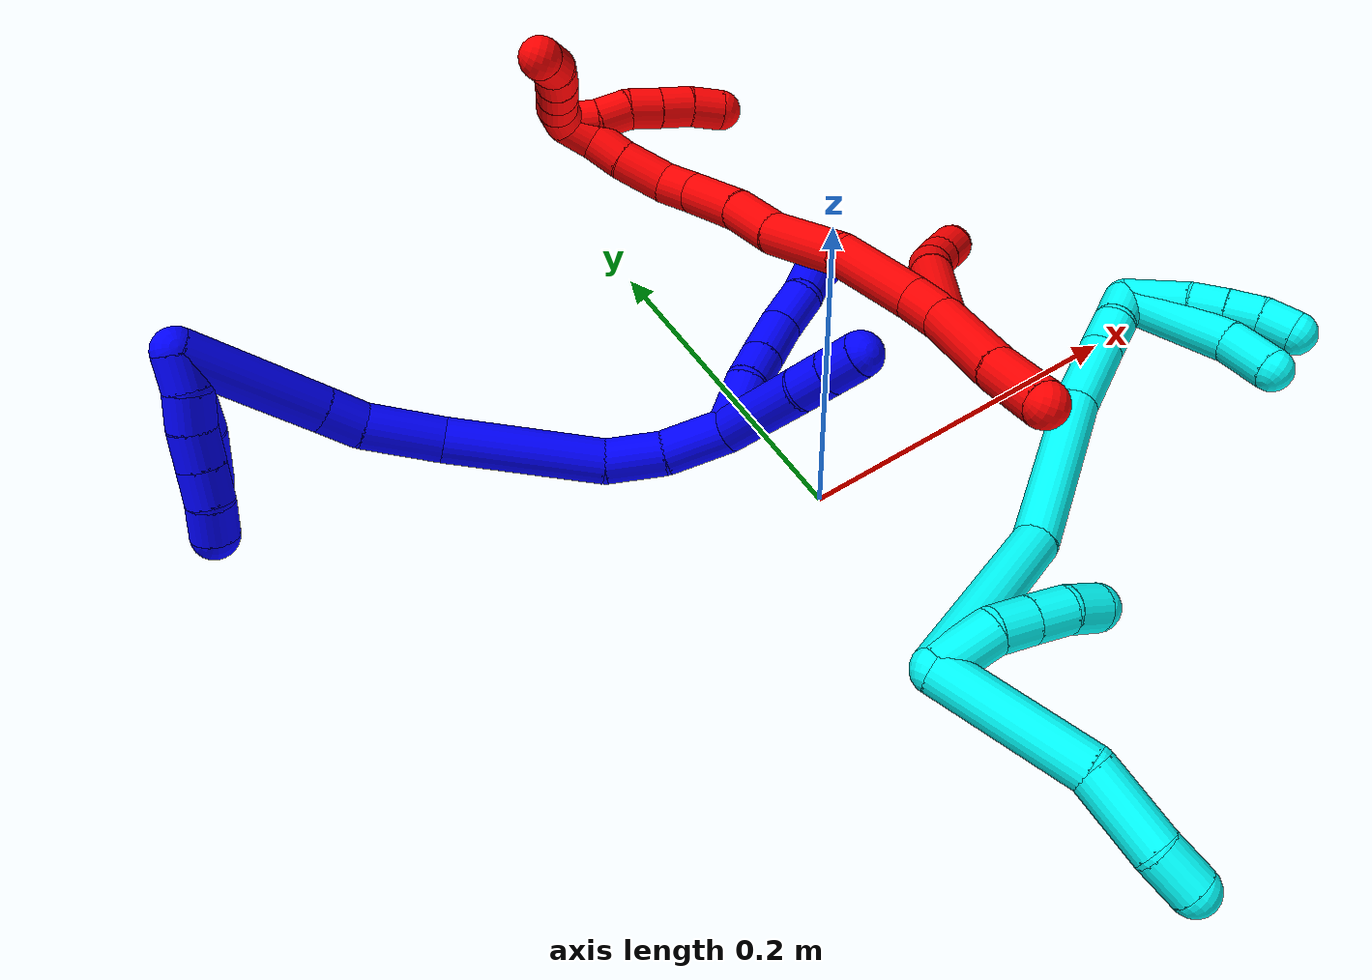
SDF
<sdf version="1.7">
 <world name="default">
  <plugin name="TubeGeneratorPlugin" filename="libtube_generator_plugin.so"/>
  <model name="photoneo_s_sensor">
   <static>1</static>
   <pose>0 0 2 1.57079 1.57079 3.14159</pose>
   <link name="link">
    <inertial><mass>0.1</mass></inertial>
    <sensor name="sensor" type="depth">
     <update_rate>30</update_rate>
     <camera>
      <horizontal_fov>1.22</horizontal_fov>
      <image><width>1920</width><height>1200</height><format>B8G8R8</format></image>
      <clip><near>0.1</near><far>4</far></clip>
      <depth_camera><output>points</output></depth_camera>
     </camera>
     <plugin name="camera_plugin" filename="libgazebo_ros_depth_camera.so">
      <baseline>0.2</baseline>
      <alwaysOn>1</alwaysOn>
      <updateRate>0.0</updateRate>
      <cameraName>camera_ir</cameraName>
      <imageTopicName>/camera/color/image_raw</imageTopicName>
      <cameraInfoTopicName>/camera/color/camera_info</cameraInfoTopicName>
      <depthImageTopicName>/camera/depth/image_raw</depthImageTopicName>
      <depthImageCameraInfoTopicName>/camera/depth/camera_info</depthImageCameraInfoTopicName>
      <pointCloudTopicName>/camera/depth/points</pointCloudTopicName>
      <frameName>fr_optical</frameName>
      <pointCloudCutoff>0.1</pointCloudCutoff>
      <pointCloudCutoffMax>2.0</pointCloudCutoffMax>
      <distortionK1>0</distortionK1>
      <distortionK2>0</distortionK2>
      <distortionK3>0</distortionK3>
      <distortionT1>0</distortionT1>
      <distortionT2>0</distortionT2>
      <CxPrime>0</CxPrime>
      <Cx>0</Cx>
      <Cy>0</Cy>
      <focalLength>0</focalLength>
      <hackBaseline>0</hackBaseline>
     </plugin>
    </sensor>
   </link>
  </model>
  <gravity>0 0 -9.8</gravity>
  <magnetic_field>6e-06 2.3e-05 -4.2e-05</magnetic_field>
  <atmosphere type="adiabatic"/>
  <physics name="default_physics" default="0" type="ode">
   <max_step_size>0.003</max_step_size>
   <real_time_factor>1</real_time_factor>
   <real_time_update_rate>1000</real_time_update_rate>
   <max_contacts>10000</max_contacts>
   <ode>
    <solver>
     <type>quick</type>
     <iters>100</iters>
     <sor>1.3</sor>
     <use_dynamic_moi_rescaling>0</use_dynamic_moi_rescaling>
    </solver>
    <constraints>
     <contact_max_correcting_vel>0</contact_max_correcting_vel>
     <contact_surface_layer>0.001</contact_surface_layer>
     <cfm>0</cfm>
     <erp>0.2</erp>
    </constraints>
   </ode>
  </physics>
  <scene><ambient>0.4 0.4 0.4 1</ambient><background>0.7 0.7 0.7 1</background><shadows>0</shadows></scene>
  <audio><device>default</device></audio>
  <spherical_coordinates>
   <surface_model>EARTH_WGS84</surface_model>
   <latitude_deg>0</latitude_deg>
   <longitude_deg>0</longitude_deg>
   <elevation>0</elevation>
   <heading_deg>0</heading_deg>
  </spherical_coordinates>
  <model name="bin">
   <static>1</static>
   <link name="bottom">
    <collision name="collision-bottom">
     <pose>0 0 -0.01 0 -0 0</pose>
     <geometry><box><size>0.8 0.6 0.02</size></box></geometry>
     <surface>
      <friction><ode><mu>100</mu><mu2>100</mu2></ode></friction>
      <contact><collide_bitmask>65535</collide_bitmask></contact>
     </surface>
    </collision>
   </link>
   <link name="west_wall">
    <collision name="collision-west_wall">
     <pose>-0.41 0 0.1 0 -0 0</pose>
     <geometry><box><size>0.02 0.6 0.2</size></box></geometry>
     <surface>
      <friction><ode><mu>100</mu><mu2>100</mu2></ode></friction>
      <contact><collide_bitmask>65535</collide_bitmask></contact>
     </surface>
    </collision>
   </link>
   <link name="east_wall">
    <collision name="collision-east_wall">
     <pose>0.41 0 0.1 0 -0 0</pose>
     <geometry><box><size>0.02 0.6 0.2</size></box></geometry>
     <surface>
      <friction><ode><mu>100</mu><mu2>100</mu2></ode></friction>
      <contact><collide_bitmask>65535</collide_bitmask></contact>
     </surface>
    </collision>
   </link>
   <link name="south_wall">
    <collision name="collision-south_wall">
     <pose>0 -0.31 0.1 0 -0 0</pose>
     <geometry><box><size>0.8 0.02 0.2</size></box></geometry>
     <surface>
      <friction><ode><mu>100</mu><mu2>100</mu2></ode></friction>
      <contact><collide_bitmask>65535</collide_bitmask></contact>
     </surface>
    </collision>
   </link>
   <link name="north_wall">
    <collision name="collision-north_wall">
     <pose>0 0.31 0.1 0 -0 0</pose>
     <geometry><box><size>0.8 0.02 0.2</size></box></geometry>
     <surface>
      <friction><ode><mu>100</mu><mu2>100</mu2></ode></friction>
      <contact><collide_bitmask>65535</collide_bitmask></contact>
     </surface>
    </collision>
   </link>
  </model>
  <model name="1">
   <static>0</static>
   <link name="1">
    <collision name="collision-cylinder-e_1_2_8">
     <pose>0.004703 -0.014976 0.002931 1.37754 0.29893 0.24669</pose>
     <geometry><cylinder><radius>0.0125</radius><length>0.031936</length></cylinder></geometry>
     <surface>
      <friction><ode><mu>1.16</mu><mu2>1.16</mu2><slip1>0</slip1><slip2>0</slip2></ode></friction>
      <contact><ode><kp>1e+06</kp><kd>1</kd><max_vel>0</max_vel><min_depth>0.001</min_depth></ode></contact>
     </surface>
    </collision>
    <visual name="visual-cylinder-e_1_2_8">
     <pose>0.004703 -0.014976 0.002931 1.37754 0.29893 0.24669</pose>
     <geometry><cylinder><radius>0.0125</radius><length>0.031936</length></cylinder></geometry>
     <material><ambient>0 0 1 1</ambient></material>
    </visual>
    <collision name="collision-cylinder-e_2_8_9">
     <pose>0.014286 -0.038787 0.009865 1.14532 0.46617 0.303757</pose>
     <geometry><cylinder><radius>0.0125</radius><length>0.021718</length></cylinder></geometry>
     <surface>
      <friction><ode><mu>1.16</mu><mu2>1.16</mu2><slip1>0</slip1><slip2>0</slip2></ode></friction>
      <contact><ode><kp>1e+06</kp><kd>1</kd><max_vel>0</max_vel><min_depth>0.001</min_depth></ode></contact>
     </surface>
    </collision>
    <visual name="visual-cylinder-e_2_8_9">
     <pose>0.014286 -0.038787 0.009865 1.14532 0.46617 0.303757</pose>
     <geometry><cylinder><radius>0.0125</radius><length>0.021718</length></cylinder></geometry>
     <material><ambient>0 0 1 1</ambient></material>
    </visual>
    <collision name="collision-cylinder-e_3_9_10">
     <pose>0.025995 -0.059913 0.019346 1.15164 0.469605 0.30814</pose>
     <geometry><cylinder><radius>0.0125</radius><length>0.030177</length></cylinder></geometry>
     <surface>
      <friction><ode><mu>1.16</mu><mu2>1.16</mu2><slip1>0</slip1><slip2>0</slip2></ode></friction>
      <contact><ode><kp>1e+06</kp><kd>1</kd><max_vel>0</max_vel><min_depth>0.001</min_depth></ode></contact>
     </surface>
    </collision>
    <visual name="visual-cylinder-e_3_9_10">
     <pose>0.025995 -0.059913 0.019346 1.15164 0.469605 0.30814</pose>
     <geometry><cylinder><radius>0.0125</radius><length>0.030177</length></cylinder></geometry>
     <material><ambient>0 0 1 1</ambient></material>
    </visual>
    <collision name="collision-cylinder-e_4_10_11">
     <pose>0.03897 -0.08351 0.025933 1.47283 0.495946 0.451224</pose>
     <geometry><cylinder><radius>0.0125</radius><length>0.025835</length></cylinder></geometry>
     <surface>
      <friction><ode><mu>1.16</mu><mu2>1.16</mu2><slip1>0</slip1><slip2>0</slip2></ode></friction>
      <contact><ode><kp>1e+06</kp><kd>1</kd><max_vel>0</max_vel><min_depth>0.001</min_depth></ode></contact>
     </surface>
    </collision>
    <visual name="visual-cylinder-e_4_10_11">
     <pose>0.03897 -0.08351 0.025933 1.47283 0.495946 0.451224</pose>
     <geometry><cylinder><radius>0.0125</radius><length>0.025835</length></cylinder></geometry>
     <material><ambient>0 0 1 1</ambient></material>
    </visual>
    <collision name="collision-cylinder-e_5_11_12">
     <pose>0.049262 -0.103096 0.031104 1.11484 0.422459 0.265756</pose>
     <geometry><cylinder><radius>0.0125</radius><length>0.020219</length></cylinder></geometry>
     <surface>
      <friction><ode><mu>1.16</mu><mu2>1.16</mu2><slip1>0</slip1><slip2>0</slip2></ode></friction>
      <contact><ode><kp>1e+06</kp><kd>1</kd><max_vel>0</max_vel><min_depth>0.001</min_depth></ode></contact>
     </surface>
    </collision>
    <visual name="visual-cylinder-e_5_11_12">
     <pose>0.049262 -0.103096 0.031104 1.11484 0.422459 0.265756</pose>
     <geometry><cylinder><radius>0.0125</radius><length>0.020219</length></cylinder></geometry>
     <material><ambient>0 0 1 1</ambient></material>
    </visual>
    <collision name="collision-cylinder-e_6_12_6">
     <pose>0.059356 -0.11726 0.040743 0.812125 0.632911 0.27975</pose>
     <geometry><cylinder><radius>0.0125</radius><length>0.020114</length></cylinder></geometry>
     <surface>
      <friction><ode><mu>1.16</mu><mu2>1.16</mu2><slip1>0</slip1><slip2>0</slip2></ode></friction>
      <contact><ode><kp>1e+06</kp><kd>1</kd><max_vel>0</max_vel><min_depth>0.001</min_depth></ode></contact>
     </surface>
    </collision>
    <visual name="visual-cylinder-e_6_12_6">
     <pose>0.059356 -0.11726 0.040743 0.812125 0.632911 0.27975</pose>
     <geometry><cylinder><radius>0.0125</radius><length>0.020114</length></cylinder></geometry>
     <material><ambient>0 0 1 1</ambient></material>
    </visual>
    <collision name="collision-cylinder-e_1_2_13">
     <pose>0.006274 -0.009044 -0.027516 2.82404 0.213323 1.17875</pose>
     <geometry><cylinder><radius>0.0125</radius><length>0.059272</length></cylinder></geometry>
     <surface>
      <friction><ode><mu>1.16</mu><mu2>1.16</mu2><slip1>0</slip1><slip2>0</slip2></ode></friction>
      <contact><ode><kp>1e+06</kp><kd>1</kd><max_vel>0</max_vel><min_depth>0.001</min_depth></ode></contact>
     </surface>
    </collision>
    <visual name="visual-cylinder-e_1_2_13">
     <pose>0.006274 -0.009044 -0.027516 2.82404 0.213323 1.17875</pose>
     <geometry><cylinder><radius>0.0125</radius><length>0.059272</length></cylinder></geometry>
     <material><ambient>0 0 1 1</ambient></material>
    </visual>
    <collision name="collision-cylinder-e_2_13_14">
     <pose>0.015828 -0.022065 -0.063719 2.71219 0.330661 1.30627</pose>
     <geometry><cylinder><radius>0.0125</radius><length>0.020203</length></cylinder></geometry>
     <surface>
      <friction><ode><mu>1.16</mu><mu2>1.16</mu2><slip1>0</slip1><slip2>0</slip2></ode></friction>
      <contact><ode><kp>1e+06</kp><kd>1</kd><max_vel>0</max_vel><min_depth>0.001</min_depth></ode></contact>
     </surface>
    </collision>
    <visual name="visual-cylinder-e_2_13_14">
     <pose>0.015828 -0.022065 -0.063719 2.71219 0.330661 1.30627</pose>
     <geometry><cylinder><radius>0.0125</radius><length>0.020203</length></cylinder></geometry>
     <material><ambient>0 0 1 1</ambient></material>
    </visual>
    <collision name="collision-cylinder-e_3_14_5">
     <pose>0.022449 -0.030139 -0.081202 2.70587 0.33168 1.29477</pose>
     <geometry><cylinder><radius>0.0125</radius><length>0.020525</length></cylinder></geometry>
     <surface>
      <friction><ode><mu>1.16</mu><mu2>1.16</mu2><slip1>0</slip1><slip2>0</slip2></ode></friction>
      <contact><ode><kp>1e+06</kp><kd>1</kd><max_vel>0</max_vel><min_depth>0.001</min_depth></ode></contact>
     </surface>
    </collision>
    <visual name="visual-cylinder-e_3_14_5">
     <pose>0.022449 -0.030139 -0.081202 2.70587 0.33168 1.29477</pose>
     <geometry><cylinder><radius>0.0125</radius><length>0.020525</length></cylinder></geometry>
     <material><ambient>0 0 1 1</ambient></material>
    </visual>
    <collision name="collision-cylinder-e_1_2_15">
     <pose>-0.013882 0.008661 0.008696 -0.783392 -0.846823 0.368076</pose>
     <geometry><cylinder><radius>0.0125</radius><length>0.037059</length></cylinder></geometry>
     <surface>
      <friction><ode><mu>1.16</mu><mu2>1.16</mu2><slip1>0</slip1><slip2>0</slip2></ode></friction>
      <contact><ode><kp>1e+06</kp><kd>1</kd><max_vel>0</max_vel><min_depth>0.001</min_depth></ode></contact>
     </surface>
    </collision>
    <visual name="visual-cylinder-e_1_2_15">
     <pose>-0.013882 0.008661 0.008696 -0.783392 -0.846823 0.368076</pose>
     <geometry><cylinder><radius>0.0125</radius><length>0.037059</length></cylinder></geometry>
     <material><ambient>0 0 1 1</ambient></material>
    </visual>
    <collision name="collision-cylinder-e_2_15_16">
     <pose>-0.041747 0.022006 0.024233 -0.600394 -1.03559 0.349075</pose>
     <geometry><cylinder><radius>0.0125</radius><length>0.032514</length></cylinder></geometry>
     <surface>
      <friction><ode><mu>1.16</mu><mu2>1.16</mu2><slip1>0</slip1><slip2>0</slip2></ode></friction>
      <contact><ode><kp>1e+06</kp><kd>1</kd><max_vel>0</max_vel><min_depth>0.001</min_depth></ode></contact>
     </surface>
    </collision>
    <visual name="visual-cylinder-e_2_15_16">
     <pose>-0.041747 0.022006 0.024233 -0.600394 -1.03559 0.349075</pose>
     <geometry><cylinder><radius>0.0125</radius><length>0.032514</length></cylinder></geometry>
     <material><ambient>0 0 1 1</ambient></material>
    </visual>
    <collision name="collision-cylinder-e_3_16_17">
     <pose>-0.097306 0.028483 0.043833 -0.139587 -1.27028 0.102954</pose>
     <geometry><cylinder><radius>0.0125</radius><length>0.087053</length></cylinder></geometry>
     <surface>
      <friction><ode><mu>1.16</mu><mu2>1.16</mu2><slip1>0</slip1><slip2>0</slip2></ode></friction>
      <contact><ode><kp>1e+06</kp><kd>1</kd><max_vel>0</max_vel><min_depth>0.001</min_depth></ode></contact>
     </surface>
    </collision>
    <visual name="visual-cylinder-e_3_16_17">
     <pose>-0.097306 0.028483 0.043833 -0.139587 -1.27028 0.102954</pose>
     <geometry><cylinder><radius>0.0125</radius><length>0.087053</length></cylinder></geometry>
     <material><ambient>0 0 1 1</ambient></material>
    </visual>
    <collision name="collision-cylinder-e_4_17_18">
     <pose>-0.16015 0.030889 0.058976 -0.251583 -1.45558 0.224391</pose>
     <geometry><cylinder><radius>0.0125</radius><length>0.04282</length></cylinder></geometry>
     <surface>
      <friction><ode><mu>1.16</mu><mu2>1.16</mu2><slip1>0</slip1><slip2>0</slip2></ode></friction>
      <contact><ode><kp>1e+06</kp><kd>1</kd><max_vel>0</max_vel><min_depth>0.001</min_depth></ode></contact>
     </surface>
    </collision>
    <visual name="visual-cylinder-e_4_17_18">
     <pose>-0.16015 0.030889 0.058976 -0.251583 -1.45558 0.224391</pose>
     <geometry><cylinder><radius>0.0125</radius><length>0.04282</length></cylinder></geometry>
     <material><ambient>0 0 1 1</ambient></material>
    </visual>
    <collision name="collision-cylinder-e_5_18_19">
     <pose>-0.192453 0.029794 0.060128 2.19591 -1.3822 -2.0339</pose>
     <geometry><cylinder><radius>0.0125</radius><length>0.022468</length></cylinder></geometry>
     <surface>
      <friction><ode><mu>1.16</mu><mu2>1.16</mu2><slip1>0</slip1><slip2>0</slip2></ode></friction>
      <contact><ode><kp>1e+06</kp><kd>1</kd><max_vel>0</max_vel><min_depth>0.001</min_depth></ode></contact>
     </surface>
    </collision>
    <visual name="visual-cylinder-e_5_18_19">
     <pose>-0.192453 0.029794 0.060128 2.19591 -1.3822 -2.0339</pose>
     <geometry><cylinder><radius>0.0125</radius><length>0.022468</length></cylinder></geometry>
     <material><ambient>0 0 1 1</ambient></material>
    </visual>
    <collision name="collision-cylinder-e_6_19_1">
     <pose>-0.24135 0.02328 0.050664 2.61311 -1.32417 -2.47337</pose>
     <geometry><cylinder><radius>0.0125</radius><length>0.078087</length></cylinder></geometry>
     <surface>
      <friction><ode><mu>1.16</mu><mu2>1.16</mu2><slip1>0</slip1><slip2>0</slip2></ode></friction>
      <contact><ode><kp>1e+06</kp><kd>1</kd><max_vel>0</max_vel><min_depth>0.001</min_depth></ode></contact>
     </surface>
    </collision>
    <visual name="visual-cylinder-e_6_19_1">
     <pose>-0.24135 0.02328 0.050664 2.61311 -1.32417 -2.47337</pose>
     <geometry><cylinder><radius>0.0125</radius><length>0.078087</length></cylinder></geometry>
     <material><ambient>0 0 1 1</ambient></material>
    </visual>
    <collision name="collision-cylinder-e_1_1_20">
     <pose>-0.274767 0.023708 0.055531 -0.380172 0.305282 -0.059182</pose>
     <geometry><cylinder><radius>0.0125</radius><length>0.029579</length></cylinder></geometry>
     <surface>
      <friction><ode><mu>1.16</mu><mu2>1.16</mu2><slip1>0</slip1><slip2>0</slip2></ode></friction>
      <contact><ode><kp>1e+06</kp><kd>1</kd><max_vel>0</max_vel><min_depth>0.001</min_depth></ode></contact>
     </surface>
    </collision>
    <visual name="visual-cylinder-e_1_1_20">
     <pose>-0.274767 0.023708 0.055531 -0.380172 0.305282 -0.059182</pose>
     <geometry><cylinder><radius>0.0125</radius><length>0.029579</length></cylinder></geometry>
     <material><ambient>0 0 1 1</ambient></material>
    </visual>
    <collision name="collision-cylinder-e_2_20_21">
     <pose>-0.263144 0.038274 0.07976 -0.697732 0.458958 -0.16953</pose>
     <geometry><cylinder><radius>0.0125</radius><length>0.032404</length></cylinder></geometry>
     <surface>
      <friction><ode><mu>1.16</mu><mu2>1.16</mu2><slip1>0</slip1><slip2>0</slip2></ode></friction>
      <contact><ode><kp>1e+06</kp><kd>1</kd><max_vel>0</max_vel><min_depth>0.001</min_depth></ode></contact>
     </surface>
    </collision>
    <visual name="visual-cylinder-e_2_20_21">
     <pose>-0.263144 0.038274 0.07976 -0.697732 0.458958 -0.16953</pose>
     <geometry><cylinder><radius>0.0125</radius><length>0.032404</length></cylinder></geometry>
     <material><ambient>0 0 1 1</ambient></material>
    </visual>
    <collision name="collision-cylinder-e_3_21_4">
     <pose>-0.250109 0.058907 0.105009 -0.674993 0.31325 -0.110721</pose>
     <geometry><cylinder><radius>0.0125</radius><length>0.038017</length></cylinder></geometry>
     <surface>
      <friction><ode><mu>1.16</mu><mu2>1.16</mu2><slip1>0</slip1><slip2>0</slip2></ode></friction>
      <contact><ode><kp>1e+06</kp><kd>1</kd><max_vel>0</max_vel><min_depth>0.001</min_depth></ode></contact>
     </surface>
    </collision>
    <visual name="visual-cylinder-e_3_21_4">
     <pose>-0.250109 0.058907 0.105009 -0.674993 0.31325 -0.110721</pose>
     <geometry><cylinder><radius>0.0125</radius><length>0.038017</length></cylinder></geometry>
     <material><ambient>0 0 1 1</ambient></material>
    </visual>
    <collision name="collision-cylinder-e_1_1_22">
     <pose>-0.274403 0.026901 0.04485 -1.29139 0.50166 -0.381406</pose>
     <geometry><cylinder><radius>0.0125</radius><length>0.02</length></cylinder></geometry>
     <surface>
      <friction><ode><mu>1.16</mu><mu2>1.16</mu2><slip1>0</slip1><slip2>0</slip2></ode></friction>
      <contact><ode><kp>1e+06</kp><kd>1</kd><max_vel>0</max_vel><min_depth>0.001</min_depth></ode></contact>
     </surface>
    </collision>
    <visual name="visual-cylinder-e_1_1_22">
     <pose>-0.274403 0.026901 0.04485 -1.29139 0.50166 -0.381406</pose>
     <geometry><cylinder><radius>0.0125</radius><length>0.02</length></cylinder></geometry>
     <material><ambient>0 0 1 1</ambient></material>
    </visual>
    <collision name="collision-cylinder-e_2_22_23">
     <pose>-0.266432 0.043832 0.051476 -1.11129 0.321729 -0.200825</pose>
     <geometry><cylinder><radius>0.0125</radius><length>0.02</length></cylinder></geometry>
     <surface>
      <friction><ode><mu>1.16</mu><mu2>1.16</mu2><slip1>0</slip1><slip2>0</slip2></ode></friction>
      <contact><ode><kp>1e+06</kp><kd>1</kd><max_vel>0</max_vel><min_depth>0.001</min_depth></ode></contact>
     </surface>
    </collision>
    <visual name="visual-cylinder-e_2_22_23">
     <pose>-0.266432 0.043832 0.051476 -1.11129 0.321729 -0.200825</pose>
     <geometry><cylinder><radius>0.0125</radius><length>0.02</length></cylinder></geometry>
     <material><ambient>0 0 1 1</ambient></material>
    </visual>
    <collision name="collision-cylinder-e_3_23_24">
     <pose>-0.258896 0.060515 0.059418 -1.14254 0.452714 -0.293926</pose>
     <geometry><cylinder><radius>0.0125</radius><length>0.02</length></cylinder></geometry>
     <surface>
      <friction><ode><mu>1.16</mu><mu2>1.16</mu2><slip1>0</slip1><slip2>0</slip2></ode></friction>
      <contact><ode><kp>1e+06</kp><kd>1</kd><max_vel>0</max_vel><min_depth>0.001</min_depth></ode></contact>
     </surface>
    </collision>
    <visual name="visual-cylinder-e_3_23_24">
     <pose>-0.258896 0.060515 0.059418 -1.14254 0.452714 -0.293926</pose>
     <geometry><cylinder><radius>0.0125</radius><length>0.02</length></cylinder></geometry>
     <material><ambient>0 0 1 1</ambient></material>
    </visual>
    <collision name="collision-cylinder-e_4_24_25">
     <pose>-0.250149 0.076892 0.066853 -1.14664 0.452628 -0.295177</pose>
     <geometry><cylinder><radius>0.0125</radius><length>0.02</length></cylinder></geometry>
     <surface>
      <friction><ode><mu>1.16</mu><mu2>1.16</mu2><slip1>0</slip1><slip2>0</slip2></ode></friction>
      <contact><ode><kp>1e+06</kp><kd>1</kd><max_vel>0</max_vel><min_depth>0.001</min_depth></ode></contact>
     </surface>
    </collision>
    <visual name="visual-cylinder-e_4_24_25">
     <pose>-0.250149 0.076892 0.066853 -1.14664 0.452628 -0.295177</pose>
     <geometry><cylinder><radius>0.0125</radius><length>0.02</length></cylinder></geometry>
     <material><ambient>0 0 1 1</ambient></material>
    </visual>
    <collision name="collision-cylinder-e_5_25_3">
     <pose>-0.242339 0.092824 0.075878 -0.96803 0.350784 -0.185794</pose>
     <geometry><cylinder><radius>0.0125</radius><length>0.02</length></cylinder></geometry>
     <surface>
      <friction><ode><mu>1.16</mu><mu2>1.16</mu2><slip1>0</slip1><slip2>0</slip2></ode></friction>
      <contact><ode><kp>1e+06</kp><kd>1</kd><max_vel>0</max_vel><min_depth>0.001</min_depth></ode></contact>
     </surface>
    </collision>
    <visual name="visual-cylinder-e_5_25_3">
     <pose>-0.242339 0.092824 0.075878 -0.96803 0.350784 -0.185794</pose>
     <geometry><cylinder><radius>0.0125</radius><length>0.02</length></cylinder></geometry>
     <material><ambient>0 0 1 1</ambient></material>
    </visual>
    <collision name="collision-sphere-3">
     <pose>-0.238903 0.10056 0.081202 0 -0 0</pose>
     <geometry><sphere><radius>0.0125</radius></sphere></geometry>
     <surface>
      <friction><ode><mu>1.16</mu><mu2>1.16</mu2><slip1>0</slip1><slip2>0</slip2></ode></friction>
      <contact><ode><kp>1e+06</kp><kd>1</kd><max_vel>0</max_vel><min_depth>0.001</min_depth></ode></contact>
     </surface>
    </collision>
    <visual name="visual-sphere-3">
     <pose>-0.238903 0.10056 0.081202 0 -0 0</pose>
     <geometry><sphere><radius>0.0125</radius></sphere></geometry>
     <material><ambient>0 0 1 1</ambient></material>
    </visual>
    <collision name="collision-sphere-25">
     <pose>-0.245775 0.085088 0.070554 0 -0 0</pose>
     <geometry><sphere><radius>0.0125</radius></sphere></geometry>
     <surface>
      <friction><ode><mu>1.16</mu><mu2>1.16</mu2><slip1>0</slip1><slip2>0</slip2></ode></friction>
      <contact><ode><kp>1e+06</kp><kd>1</kd><max_vel>0</max_vel><min_depth>0.001</min_depth></ode></contact>
     </surface>
    </collision>
    <visual name="visual-sphere-25">
     <pose>-0.245775 0.085088 0.070554 0 -0 0</pose>
     <geometry><sphere><radius>0.0125</radius></sphere></geometry>
     <material><ambient>0 0 1 1</ambient></material>
    </visual>
    <collision name="collision-sphere-24">
     <pose>-0.254522 0.068696 0.063152 0 -0 0</pose>
     <geometry><sphere><radius>0.0125</radius></sphere></geometry>
     <surface>
      <friction><ode><mu>1.16</mu><mu2>1.16</mu2><slip1>0</slip1><slip2>0</slip2></ode></friction>
      <contact><ode><kp>1e+06</kp><kd>1</kd><max_vel>0</max_vel><min_depth>0.001</min_depth></ode></contact>
     </surface>
    </collision>
    <visual name="visual-sphere-24">
     <pose>-0.254522 0.068696 0.063152 0 -0 0</pose>
     <geometry><sphere><radius>0.0125</radius></sphere></geometry>
     <material><ambient>0 0 1 1</ambient></material>
    </visual>
    <collision name="collision-sphere-23">
     <pose>-0.26327 0.052335 0.055683 0 -0 0</pose>
     <geometry><sphere><radius>0.0125</radius></sphere></geometry>
     <surface>
      <friction><ode><mu>1.16</mu><mu2>1.16</mu2><slip1>0</slip1><slip2>0</slip2></ode></friction>
      <contact><ode><kp>1e+06</kp><kd>1</kd><max_vel>0</max_vel><min_depth>0.001</min_depth></ode></contact>
     </surface>
    </collision>
    <visual name="visual-sphere-23">
     <pose>-0.26327 0.052335 0.055683 0 -0 0</pose>
     <geometry><sphere><radius>0.0125</radius></sphere></geometry>
     <material><ambient>0 0 1 1</ambient></material>
    </visual>
    <collision name="collision-sphere-22">
     <pose>-0.269594 0.035329 0.047268 0 -0 0</pose>
     <geometry><sphere><radius>0.0125</radius></sphere></geometry>
     <surface>
      <friction><ode><mu>1.16</mu><mu2>1.16</mu2><slip1>0</slip1><slip2>0</slip2></ode></friction>
      <contact><ode><kp>1e+06</kp><kd>1</kd><max_vel>0</max_vel><min_depth>0.001</min_depth></ode></contact>
     </surface>
    </collision>
    <visual name="visual-sphere-22">
     <pose>-0.269594 0.035329 0.047268 0 -0 0</pose>
     <geometry><sphere><radius>0.0125</radius></sphere></geometry>
     <material><ambient>0 0 1 1</ambient></material>
    </visual>
    <collision name="collision-sphere-4">
     <pose>-0.244251 0.070207 0.119127 0 -0 0</pose>
     <geometry><sphere><radius>0.0125</radius></sphere></geometry>
     <surface>
      <friction><ode><mu>1.16</mu><mu2>1.16</mu2><slip1>0</slip1><slip2>0</slip2></ode></friction>
      <contact><ode><kp>1e+06</kp><kd>1</kd><max_vel>0</max_vel><min_depth>0.001</min_depth></ode></contact>
     </surface>
    </collision>
    <visual name="visual-sphere-4">
     <pose>-0.244251 0.070207 0.119127 0 -0 0</pose>
     <geometry><sphere><radius>0.0125</radius></sphere></geometry>
     <material><ambient>0 0 1 1</ambient></material>
    </visual>
    <collision name="collision-sphere-21">
     <pose>-0.255966 0.047606 0.090891 0 -0 0</pose>
     <geometry><sphere><radius>0.0125</radius></sphere></geometry>
     <surface>
      <friction><ode><mu>1.16</mu><mu2>1.16</mu2><slip1>0</slip1><slip2>0</slip2></ode></friction>
      <contact><ode><kp>1e+06</kp><kd>1</kd><max_vel>0</max_vel><min_depth>0.001</min_depth></ode></contact>
     </surface>
    </collision>
    <visual name="visual-sphere-21">
     <pose>-0.255966 0.047606 0.090891 0 -0 0</pose>
     <geometry><sphere><radius>0.0125</radius></sphere></geometry>
     <material><ambient>0 0 1 1</ambient></material>
    </visual>
    <collision name="collision-sphere-20">
     <pose>-0.270321 0.028942 0.068629 0 -0 0</pose>
     <geometry><sphere><radius>0.0125</radius></sphere></geometry>
     <surface>
      <friction><ode><mu>1.16</mu><mu2>1.16</mu2><slip1>0</slip1><slip2>0</slip2></ode></friction>
      <contact><ode><kp>1e+06</kp><kd>1</kd><max_vel>0</max_vel><min_depth>0.001</min_depth></ode></contact>
     </surface>
    </collision>
    <visual name="visual-sphere-20">
     <pose>-0.270321 0.028942 0.068629 0 -0 0</pose>
     <geometry><sphere><radius>0.0125</radius></sphere></geometry>
     <material><ambient>0 0 1 1</ambient></material>
    </visual>
    <collision name="collision-sphere-12">
     <pose>0.053407 -0.111375 0.035165 0 -0 0</pose>
     <geometry><sphere><radius>0.0125</radius></sphere></geometry>
     <surface>
      <friction><ode><mu>1.16</mu><mu2>1.16</mu2><slip1>0</slip1><slip2>0</slip2></ode></friction>
      <contact><ode><kp>1e+06</kp><kd>1</kd><max_vel>0</max_vel><min_depth>0.001</min_depth></ode></contact>
     </surface>
    </collision>
    <visual name="visual-sphere-12">
     <pose>0.053407 -0.111375 0.035165 0 -0 0</pose>
     <geometry><sphere><radius>0.0125</radius></sphere></geometry>
     <material><ambient>0 0 1 1</ambient></material>
    </visual>
    <collision name="collision-sphere-11">
     <pose>0.045117 -0.094817 0.027044 0 -0 0</pose>
     <geometry><sphere><radius>0.0125</radius></sphere></geometry>
     <surface>
      <friction><ode><mu>1.16</mu><mu2>1.16</mu2><slip1>0</slip1><slip2>0</slip2></ode></friction>
      <contact><ode><kp>1e+06</kp><kd>1</kd><max_vel>0</max_vel><min_depth>0.001</min_depth></ode></contact>
     </surface>
    </collision>
    <visual name="visual-sphere-11">
     <pose>0.045117 -0.094817 0.027044 0 -0 0</pose>
     <geometry><sphere><radius>0.0125</radius></sphere></geometry>
     <material><ambient>0 0 1 1</ambient></material>
    </visual>
    <collision name="collision-sphere-10">
     <pose>0.032823 -0.072203 0.024822 0 -0 0</pose>
     <geometry><sphere><radius>0.0125</radius></sphere></geometry>
     <surface>
      <friction><ode><mu>1.16</mu><mu2>1.16</mu2><slip1>0</slip1><slip2>0</slip2></ode></friction>
      <contact><ode><kp>1e+06</kp><kd>1</kd><max_vel>0</max_vel><min_depth>0.001</min_depth></ode></contact>
     </surface>
    </collision>
    <visual name="visual-sphere-10">
     <pose>0.032823 -0.072203 0.024822 0 -0 0</pose>
     <geometry><sphere><radius>0.0125</radius></sphere></geometry>
     <material><ambient>0 0 1 1</ambient></material>
    </visual>
    <collision name="collision-sphere-9">
     <pose>0.019167 -0.047623 0.013869 0 -0 0</pose>
     <geometry><sphere><radius>0.0125</radius></sphere></geometry>
     <surface>
      <friction><ode><mu>1.16</mu><mu2>1.16</mu2><slip1>0</slip1><slip2>0</slip2></ode></friction>
      <contact><ode><kp>1e+06</kp><kd>1</kd><max_vel>0</max_vel><min_depth>0.001</min_depth></ode></contact>
     </surface>
    </collision>
    <visual name="visual-sphere-9">
     <pose>0.019167 -0.047623 0.013869 0 -0 0</pose>
     <geometry><sphere><radius>0.0125</radius></sphere></geometry>
     <material><ambient>0 0 1 1</ambient></material>
    </visual>
    <collision name="collision-sphere-2">
     <geometry><sphere><radius>0.0125</radius></sphere></geometry>
     <surface>
      <friction><ode><mu>1.16</mu><mu2>1.16</mu2><slip1>0</slip1><slip2>0</slip2></ode></friction>
      <contact><ode><kp>1e+06</kp><kd>1</kd><max_vel>0</max_vel><min_depth>0.001</min_depth></ode></contact>
     </surface>
    </collision>
    <visual name="visual-sphere-2">
     <geometry><sphere><radius>0.0125</radius></sphere></geometry>
     <material><ambient>0 0 1 1</ambient></material>
    </visual>
    <collision name="collision-sphere-19">
     <pose>-0.203488 0.028086 0.058895 0 -0 0</pose>
     <geometry><sphere><radius>0.0125</radius></sphere></geometry>
     <surface>
      <friction><ode><mu>1.16</mu><mu2>1.16</mu2><slip1>0</slip1><slip2>0</slip2></ode></friction>
      <contact><ode><kp>1e+06</kp><kd>1</kd><max_vel>0</max_vel><min_depth>0.001</min_depth></ode></contact>
     </surface>
    </collision>
    <visual name="visual-sphere-19">
     <pose>-0.203488 0.028086 0.058895 0 -0 0</pose>
     <geometry><sphere><radius>0.0125</radius></sphere></geometry>
     <material><ambient>0 0 1 1</ambient></material>
    </visual>
    <collision name="collision-sphere-8">
     <pose>0.009405 -0.029952 0.005862 0 -0 0</pose>
     <geometry><sphere><radius>0.0125</radius></sphere></geometry>
     <surface>
      <friction><ode><mu>1.16</mu><mu2>1.16</mu2><slip1>0</slip1><slip2>0</slip2></ode></friction>
      <contact><ode><kp>1e+06</kp><kd>1</kd><max_vel>0</max_vel><min_depth>0.001</min_depth></ode></contact>
     </surface>
    </collision>
    <visual name="visual-sphere-8">
     <pose>0.009405 -0.029952 0.005862 0 -0 0</pose>
     <geometry><sphere><radius>0.0125</radius></sphere></geometry>
     <material><ambient>0 0 1 1</ambient></material>
    </visual>
    <collision name="collision-sphere-6">
     <pose>0.065304 -0.123145 0.046322 0 -0 0</pose>
     <geometry><sphere><radius>0.0125</radius></sphere></geometry>
     <surface>
      <friction><ode><mu>1.16</mu><mu2>1.16</mu2><slip1>0</slip1><slip2>0</slip2></ode></friction>
      <contact><ode><kp>1e+06</kp><kd>1</kd><max_vel>0</max_vel><min_depth>0.001</min_depth></ode></contact>
     </surface>
    </collision>
    <visual name="visual-sphere-6">
     <pose>0.065304 -0.123145 0.046322 0 -0 0</pose>
     <geometry><sphere><radius>0.0125</radius></sphere></geometry>
     <material><ambient>0 0 1 1</ambient></material>
    </visual>
    <collision name="collision-sphere-13">
     <pose>0.012548 -0.018088 -0.055032 0 -0 0</pose>
     <geometry><sphere><radius>0.0125</radius></sphere></geometry>
     <surface>
      <friction><ode><mu>1.16</mu><mu2>1.16</mu2><slip1>0</slip1><slip2>0</slip2></ode></friction>
      <contact><ode><kp>1e+06</kp><kd>1</kd><max_vel>0</max_vel><min_depth>0.001</min_depth></ode></contact>
     </surface>
    </collision>
    <visual name="visual-sphere-13">
     <pose>0.012548 -0.018088 -0.055032 0 -0 0</pose>
     <geometry><sphere><radius>0.0125</radius></sphere></geometry>
     <material><ambient>0 0 1 1</ambient></material>
    </visual>
    <collision name="collision-sphere-14">
     <pose>0.019108 -0.026043 -0.072406 0 -0 0</pose>
     <geometry><sphere><radius>0.0125</radius></sphere></geometry>
     <surface>
      <friction><ode><mu>1.16</mu><mu2>1.16</mu2><slip1>0</slip1><slip2>0</slip2></ode></friction>
      <contact><ode><kp>1e+06</kp><kd>1</kd><max_vel>0</max_vel><min_depth>0.001</min_depth></ode></contact>
     </surface>
    </collision>
    <visual name="visual-sphere-14">
     <pose>0.019108 -0.026043 -0.072406 0 -0 0</pose>
     <geometry><sphere><radius>0.0125</radius></sphere></geometry>
     <material><ambient>0 0 1 1</ambient></material>
    </visual>
    <collision name="collision-sphere-5">
     <pose>0.025791 -0.034234 -0.089999 0 -0 0</pose>
     <geometry><sphere><radius>0.0125</radius></sphere></geometry>
     <surface>
      <friction><ode><mu>1.16</mu><mu2>1.16</mu2><slip1>0</slip1><slip2>0</slip2></ode></friction>
      <contact><ode><kp>1e+06</kp><kd>1</kd><max_vel>0</max_vel><min_depth>0.001</min_depth></ode></contact>
     </surface>
    </collision>
    <visual name="visual-sphere-5">
     <pose>0.025791 -0.034234 -0.089999 0 -0 0</pose>
     <geometry><sphere><radius>0.0125</radius></sphere></geometry>
     <material><ambient>0 0 1 1</ambient></material>
    </visual>
    <collision name="collision-sphere-15">
     <pose>-0.027764 0.017322 0.017392 0 -0 0</pose>
     <geometry><sphere><radius>0.0125</radius></sphere></geometry>
     <surface>
      <friction><ode><mu>1.16</mu><mu2>1.16</mu2><slip1>0</slip1><slip2>0</slip2></ode></friction>
      <contact><ode><kp>1e+06</kp><kd>1</kd><max_vel>0</max_vel><min_depth>0.001</min_depth></ode></contact>
     </surface>
    </collision>
    <visual name="visual-sphere-15">
     <pose>-0.027764 0.017322 0.017392 0 -0 0</pose>
     <geometry><sphere><radius>0.0125</radius></sphere></geometry>
     <material><ambient>0 0 1 1</ambient></material>
    </visual>
    <collision name="collision-sphere-16">
     <pose>-0.055731 0.026691 0.031074 0 -0 0</pose>
     <geometry><sphere><radius>0.0125</radius></sphere></geometry>
     <surface>
      <friction><ode><mu>1.16</mu><mu2>1.16</mu2><slip1>0</slip1><slip2>0</slip2></ode></friction>
      <contact><ode><kp>1e+06</kp><kd>1</kd><max_vel>0</max_vel><min_depth>0.001</min_depth></ode></contact>
     </surface>
    </collision>
    <visual name="visual-sphere-16">
     <pose>-0.055731 0.026691 0.031074 0 -0 0</pose>
     <geometry><sphere><radius>0.0125</radius></sphere></geometry>
     <material><ambient>0 0 1 1</ambient></material>
    </visual>
    <collision name="collision-sphere-17">
     <pose>-0.138882 0.030276 0.056592 0 -0 0</pose>
     <geometry><sphere><radius>0.0125</radius></sphere></geometry>
     <surface>
      <friction><ode><mu>1.16</mu><mu2>1.16</mu2><slip1>0</slip1><slip2>0</slip2></ode></friction>
      <contact><ode><kp>1e+06</kp><kd>1</kd><max_vel>0</max_vel><min_depth>0.001</min_depth></ode></contact>
     </surface>
    </collision>
    <visual name="visual-sphere-17">
     <pose>-0.138882 0.030276 0.056592 0 -0 0</pose>
     <geometry><sphere><radius>0.0125</radius></sphere></geometry>
     <material><ambient>0 0 1 1</ambient></material>
    </visual>
    <collision name="collision-sphere-18">
     <pose>-0.181418 0.031501 0.06136 0 -0 0</pose>
     <geometry><sphere><radius>0.0125</radius></sphere></geometry>
     <surface>
      <friction><ode><mu>1.16</mu><mu2>1.16</mu2><slip1>0</slip1><slip2>0</slip2></ode></friction>
      <contact><ode><kp>1e+06</kp><kd>1</kd><max_vel>0</max_vel><min_depth>0.001</min_depth></ode></contact>
     </surface>
    </collision>
    <visual name="visual-sphere-18">
     <pose>-0.181418 0.031501 0.06136 0 -0 0</pose>
     <geometry><sphere><radius>0.0125</radius></sphere></geometry>
     <material><ambient>0 0 1 1</ambient></material>
    </visual>
    <collision name="collision-sphere-1">
     <pose>-0.279212 0.018473 0.042432 0 -0 0</pose>
     <geometry><sphere><radius>0.0125</radius></sphere></geometry>
     <surface>
      <friction><ode><mu>1.16</mu><mu2>1.16</mu2><slip1>0</slip1><slip2>0</slip2></ode></friction>
      <contact><ode><kp>1e+06</kp><kd>1</kd><max_vel>0</max_vel><min_depth>0.001</min_depth></ode></contact>
     </surface>
    </collision>
    <visual name="visual-sphere-1">
     <pose>-0.279212 0.018473 0.042432 0 -0 0</pose>
     <geometry><sphere><radius>0.0125</radius></sphere></geometry>
     <material><ambient>0 0 1 1</ambient></material>
    </visual>
    <inertial>
     <pose>-0.115711 0.008262 0.03383 0 -0 0</pose>
     <mass>0.75</mass>
     <inertia><ixx>6.4e-05</ixx><ixy>0</ixy><ixz>0</ixz><iyy>0.000152</iyy><iyz>0</iyz><izz>0.00011</izz></inertia>
    </inertial>
   </link>
   <pose>-0.023875 0.05333 0.021612 -2.60544 0.47909 -0.493326</pose>
  </model>
  <model name="2">
   <static>0</static>
   <link name="2">
    <collision name="collision-cylinder-e_1_2_8">
     <pose>0.028579 0.020404 -0.007538 -1.92469 0.920203 -1.23668</pose>
     <geometry><cylinder><radius>0.0125</radius><length>0.07183</length></cylinder></geometry>
     <surface>
      <friction><ode><mu>1.16</mu><mu2>1.16</mu2><slip1>0</slip1><slip2>0</slip2></ode></friction>
      <contact><ode><kp>1e+06</kp><kd>1</kd><max_vel>0</max_vel><min_depth>0.001</min_depth></ode></contact>
     </surface>
    </collision>
    <visual name="visual-cylinder-e_1_2_8">
     <pose>0.028579 0.020404 -0.007538 -1.92469 0.920203 -1.23668</pose>
     <geometry><cylinder><radius>0.0125</radius><length>0.07183</length></cylinder></geometry>
     <material><ambient>1 0 0 1</ambient></material>
    </visual>
    <collision name="collision-cylinder-e_2_8_9">
     <pose>0.067063 0.049571 -0.019511 -2.0393 0.789745 -1.19163</pose>
     <geometry><cylinder><radius>0.0125</radius><length>0.027898</length></cylinder></geometry>
     <surface>
      <friction><ode><mu>1.16</mu><mu2>1.16</mu2><slip1>0</slip1><slip2>0</slip2></ode></friction>
      <contact><ode><kp>1e+06</kp><kd>1</kd><max_vel>0</max_vel><min_depth>0.001</min_depth></ode></contact>
     </surface>
    </collision>
    <visual name="visual-cylinder-e_2_8_9">
     <pose>0.067063 0.049571 -0.019511 -2.0393 0.789745 -1.19163</pose>
     <geometry><cylinder><radius>0.0125</radius><length>0.027898</length></cylinder></geometry>
     <material><ambient>1 0 0 1</ambient></material>
    </visual>
    <collision name="collision-cylinder-e_3_9_10">
     <pose>0.085729 0.06385 -0.029897 -2.39412 0.823559 -1.67826</pose>
     <geometry><cylinder><radius>0.0125</radius><length>0.023882</length></cylinder></geometry>
     <surface>
      <friction><ode><mu>1.16</mu><mu2>1.16</mu2><slip1>0</slip1><slip2>0</slip2></ode></friction>
      <contact><ode><kp>1e+06</kp><kd>1</kd><max_vel>0</max_vel><min_depth>0.001</min_depth></ode></contact>
     </surface>
    </collision>
    <visual name="visual-cylinder-e_3_9_10">
     <pose>0.085729 0.06385 -0.029897 -2.39412 0.823559 -1.67826</pose>
     <geometry><cylinder><radius>0.0125</radius><length>0.023882</length></cylinder></geometry>
     <material><ambient>1 0 0 1</ambient></material>
    </visual>
    <collision name="collision-cylinder-e_4_10_6">
     <pose>0.104514 0.074092 -0.04301 -2.5583 0.862954 -1.98597</pose>
     <geometry><cylinder><radius>0.0125</radius><length>0.026389</length></cylinder></geometry>
     <surface>
      <friction><ode><mu>1.16</mu><mu2>1.16</mu2><slip1>0</slip1><slip2>0</slip2></ode></friction>
      <contact><ode><kp>1e+06</kp><kd>1</kd><max_vel>0</max_vel><min_depth>0.001</min_depth></ode></contact>
     </surface>
    </collision>
    <visual name="visual-cylinder-e_4_10_6">
     <pose>0.104514 0.074092 -0.04301 -2.5583 0.862954 -1.98597</pose>
     <geometry><cylinder><radius>0.0125</radius><length>0.026389</length></cylinder></geometry>
     <material><ambient>1 0 0 1</ambient></material>
    </visual>
    <collision name="collision-cylinder-e_1_2_11">
     <pose>-0.022713 -0.01866 -0.005067 1.83596 -0.865538 -1.08695</pose>
     <geometry><cylinder><radius>0.0125</radius><length>0.059657</length></cylinder></geometry>
     <surface>
      <friction><ode><mu>1.16</mu><mu2>1.16</mu2><slip1>0</slip1><slip2>0</slip2></ode></friction>
      <contact><ode><kp>1e+06</kp><kd>1</kd><max_vel>0</max_vel><min_depth>0.001</min_depth></ode></contact>
     </surface>
    </collision>
    <visual name="visual-cylinder-e_1_2_11">
     <pose>-0.022713 -0.01866 -0.005067 1.83596 -0.865538 -1.08695</pose>
     <geometry><cylinder><radius>0.0125</radius><length>0.059657</length></cylinder></geometry>
     <material><ambient>1 0 0 1</ambient></material>
    </visual>
    <collision name="collision-cylinder-e_2_11_5">
     <pose>-0.059827 -0.050758 -0.014483 1.88378 -0.795124 -1.04706</pose>
     <geometry><cylinder><radius>0.0125</radius><length>0.040343</length></cylinder></geometry>
     <surface>
      <friction><ode><mu>1.16</mu><mu2>1.16</mu2><slip1>0</slip1><slip2>0</slip2></ode></friction>
      <contact><ode><kp>1e+06</kp><kd>1</kd><max_vel>0</max_vel><min_depth>0.001</min_depth></ode></contact>
     </surface>
    </collision>
    <visual name="visual-cylinder-e_2_11_5">
     <pose>-0.059827 -0.050758 -0.014483 1.88378 -0.795124 -1.04706</pose>
     <geometry><cylinder><radius>0.0125</radius><length>0.040343</length></cylinder></geometry>
     <material><ambient>1 0 0 1</ambient></material>
    </visual>
    <collision name="collision-cylinder-e_1_2_12">
     <pose>0.007996 0.006632 0.005694 -0.861333 0.740938 -0.353169</pose>
     <geometry><cylinder><radius>0.0125</radius><length>0.023693</length></cylinder></geometry>
     <surface>
      <friction><ode><mu>1.16</mu><mu2>1.16</mu2><slip1>0</slip1><slip2>0</slip2></ode></friction>
      <contact><ode><kp>1e+06</kp><kd>1</kd><max_vel>0</max_vel><min_depth>0.001</min_depth></ode></contact>
     </surface>
    </collision>
    <visual name="visual-cylinder-e_1_2_12">
     <pose>0.007996 0.006632 0.005694 -0.861333 0.740938 -0.353169</pose>
     <geometry><cylinder><radius>0.0125</radius><length>0.023693</length></cylinder></geometry>
     <material><ambient>1 0 0 1</ambient></material>
    </visual>
    <collision name="collision-cylinder-e_2_12_13">
     <pose>0.030624 0.0253 0.027964 -0.628043 0.620237 -0.207402</pose>
     <geometry><cylinder><radius>0.0125</radius><length>0.050346</length></cylinder></geometry>
     <surface>
      <friction><ode><mu>1.16</mu><mu2>1.16</mu2><slip1>0</slip1><slip2>0</slip2></ode></friction>
      <contact><ode><kp>1e+06</kp><kd>1</kd><max_vel>0</max_vel><min_depth>0.001</min_depth></ode></contact>
     </surface>
    </collision>
    <visual name="visual-cylinder-e_2_12_13">
     <pose>0.030624 0.0253 0.027964 -0.628043 0.620237 -0.207402</pose>
     <geometry><cylinder><radius>0.0125</radius><length>0.050346</length></cylinder></geometry>
     <material><ambient>1 0 0 1</ambient></material>
    </visual>
    <collision name="collision-cylinder-e_3_13_14">
     <pose>0.059147 0.056963 0.056874 -1.00974 0.539874 -0.303473</pose>
     <geometry><cylinder><radius>0.0125</radius><length>0.054052</length></cylinder></geometry>
     <surface>
      <friction><ode><mu>1.16</mu><mu2>1.16</mu2><slip1>0</slip1><slip2>0</slip2></ode></friction>
      <contact><ode><kp>1e+06</kp><kd>1</kd><max_vel>0</max_vel><min_depth>0.001</min_depth></ode></contact>
     </surface>
    </collision>
    <visual name="visual-cylinder-e_3_13_14">
     <pose>0.059147 0.056963 0.056874 -1.00974 0.539874 -0.303473</pose>
     <geometry><cylinder><radius>0.0125</radius><length>0.054052</length></cylinder></geometry>
     <material><ambient>1 0 0 1</ambient></material>
    </visual>
    <collision name="collision-cylinder-e_4_14_15">
     <pose>0.084625 0.087228 0.076926 -0.943092 0.722558 -0.38069</pose>
     <geometry><cylinder><radius>0.0125</radius><length>0.035038</length></cylinder></geometry>
     <surface>
      <friction><ode><mu>1.16</mu><mu2>1.16</mu2><slip1>0</slip1><slip2>0</slip2></ode></friction>
      <contact><ode><kp>1e+06</kp><kd>1</kd><max_vel>0</max_vel><min_depth>0.001</min_depth></ode></contact>
     </surface>
    </collision>
    <visual name="visual-cylinder-e_4_14_15">
     <pose>0.084625 0.087228 0.076926 -0.943092 0.722558 -0.38069</pose>
     <geometry><cylinder><radius>0.0125</radius><length>0.035038</length></cylinder></geometry>
     <material><ambient>1 0 0 1</ambient></material>
    </visual>
    <collision name="collision-cylinder-e_5_15_16">
     <pose>0.107904 0.112598 0.094088 -1.00078 0.589049 -0.328753</pose>
     <geometry><cylinder><radius>0.0125</radius><length>0.042096</length></cylinder></geometry>
     <surface>
      <friction><ode><mu>1.16</mu><mu2>1.16</mu2><slip1>0</slip1><slip2>0</slip2></ode></friction>
      <contact><ode><kp>1e+06</kp><kd>1</kd><max_vel>0</max_vel><min_depth>0.001</min_depth></ode></contact>
     </surface>
    </collision>
    <visual name="visual-cylinder-e_5_15_16">
     <pose>0.107904 0.112598 0.094088 -1.00078 0.589049 -0.328753</pose>
     <geometry><cylinder><radius>0.0125</radius><length>0.042096</length></cylinder></geometry>
     <material><ambient>1 0 0 1</ambient></material>
    </visual>
    <collision name="collision-cylinder-e_6_16_17">
     <pose>0.124157 0.133412 0.11122 -0.669144 0.435435 -0.153511</pose>
     <geometry><cylinder><radius>0.0125</radius><length>0.021621</length></cylinder></geometry>
     <surface>
      <friction><ode><mu>1.16</mu><mu2>1.16</mu2><slip1>0</slip1><slip2>0</slip2></ode></friction>
      <contact><ode><kp>1e+06</kp><kd>1</kd><max_vel>0</max_vel><min_depth>0.001</min_depth></ode></contact>
     </surface>
    </collision>
    <visual name="visual-cylinder-e_6_16_17">
     <pose>0.124157 0.133412 0.11122 -0.669144 0.435435 -0.153511</pose>
     <geometry><cylinder><radius>0.0125</radius><length>0.021621</length></cylinder></geometry>
     <material><ambient>1 0 0 1</ambient></material>
    </visual>
    <collision name="collision-cylinder-e_7_17_18">
     <pose>0.134511 0.143679 0.132379 -0.301328 0.389688 -0.059902</pose>
     <geometry><cylinder><radius>0.0125</radius><length>0.030499</length></cylinder></geometry>
     <surface>
      <friction><ode><mu>1.16</mu><mu2>1.16</mu2><slip1>0</slip1><slip2>0</slip2></ode></friction>
      <contact><ode><kp>1e+06</kp><kd>1</kd><max_vel>0</max_vel><min_depth>0.001</min_depth></ode></contact>
     </surface>
    </collision>
    <visual name="visual-cylinder-e_7_17_18">
     <pose>0.134511 0.143679 0.132379 -0.301328 0.389688 -0.059902</pose>
     <geometry><cylinder><radius>0.0125</radius><length>0.030499</length></cylinder></geometry>
     <material><ambient>1 0 0 1</ambient></material>
    </visual>
    <collision name="collision-cylinder-e_8_18_19">
     <pose>0.145523 0.150186 0.155131 -0.24501 0.499452 -0.062784</pose>
     <geometry><cylinder><radius>0.0125</radius><length>0.021795</length></cylinder></geometry>
     <surface>
      <friction><ode><mu>1.16</mu><mu2>1.16</mu2><slip1>0</slip1><slip2>0</slip2></ode></friction>
      <contact><ode><kp>1e+06</kp><kd>1</kd><max_vel>0</max_vel><min_depth>0.001</min_depth></ode></contact>
     </surface>
    </collision>
    <visual name="visual-cylinder-e_8_18_19">
     <pose>0.145523 0.150186 0.155131 -0.24501 0.499452 -0.062784</pose>
     <geometry><cylinder><radius>0.0125</radius><length>0.021795</length></cylinder></geometry>
     <material><ambient>1 0 0 1</ambient></material>
    </visual>
    <collision name="collision-cylinder-e_9_19_1">
     <pose>0.153586 0.153452 0.174401 -0.094417 0.276106 -0.013128</pose>
     <geometry><cylinder><radius>0.0125</radius><length>0.020859</length></cylinder></geometry>
     <surface>
      <friction><ode><mu>1.16</mu><mu2>1.16</mu2><slip1>0</slip1><slip2>0</slip2></ode></friction>
      <contact><ode><kp>1e+06</kp><kd>1</kd><max_vel>0</max_vel><min_depth>0.001</min_depth></ode></contact>
     </surface>
    </collision>
    <visual name="visual-cylinder-e_9_19_1">
     <pose>0.153586 0.153452 0.174401 -0.094417 0.276106 -0.013128</pose>
     <geometry><cylinder><radius>0.0125</radius><length>0.020859</length></cylinder></geometry>
     <material><ambient>1 0 0 1</ambient></material>
    </visual>
    <collision name="collision-cylinder-e_1_1_20">
     <pose>0.154113 0.146201 0.189629 1.00214 -0.233778 -0.128447</pose>
     <geometry><cylinder><radius>0.0125</radius><length>0.02</length></cylinder></geometry>
     <surface>
      <friction><ode><mu>1.16</mu><mu2>1.16</mu2><slip1>0</slip1><slip2>0</slip2></ode></friction>
      <contact><ode><kp>1e+06</kp><kd>1</kd><max_vel>0</max_vel><min_depth>0.001</min_depth></ode></contact>
     </surface>
    </collision>
    <visual name="visual-cylinder-e_1_1_20">
     <pose>0.154113 0.146201 0.189629 1.00214 -0.233778 -0.128447</pose>
     <geometry><cylinder><radius>0.0125</radius><length>0.02</length></cylinder></geometry>
     <material><ambient>1 0 0 1</ambient></material>
    </visual>
    <collision name="collision-cylinder-e_2_20_21">
     <pose>0.148747 0.128842 0.197467 1.29444 -0.309833 -0.234986</pose>
     <geometry><cylinder><radius>0.0125</radius><length>0.02</length></cylinder></geometry>
     <surface>
      <friction><ode><mu>1.16</mu><mu2>1.16</mu2><slip1>0</slip1><slip2>0</slip2></ode></friction>
      <contact><ode><kp>1e+06</kp><kd>1</kd><max_vel>0</max_vel><min_depth>0.001</min_depth></ode></contact>
     </surface>
    </collision>
    <visual name="visual-cylinder-e_2_20_21">
     <pose>0.148747 0.128842 0.197467 1.29444 -0.309833 -0.234986</pose>
     <geometry><cylinder><radius>0.0125</radius><length>0.02</length></cylinder></geometry>
     <material><ambient>1 0 0 1</ambient></material>
    </visual>
    <collision name="collision-cylinder-e_3_21_22">
     <pose>0.142553 0.110586 0.20279 1.2797 -0.319953 -0.239052</pose>
     <geometry><cylinder><radius>0.0125</radius><length>0.02</length></cylinder></geometry>
     <surface>
      <friction><ode><mu>1.16</mu><mu2>1.16</mu2><slip1>0</slip1><slip2>0</slip2></ode></friction>
      <contact><ode><kp>1e+06</kp><kd>1</kd><max_vel>0</max_vel><min_depth>0.001</min_depth></ode></contact>
     </surface>
    </collision>
    <visual name="visual-cylinder-e_3_21_22">
     <pose>0.142553 0.110586 0.20279 1.2797 -0.319953 -0.239052</pose>
     <geometry><cylinder><radius>0.0125</radius><length>0.02</length></cylinder></geometry>
     <material><ambient>1 0 0 1</ambient></material>
    </visual>
    <collision name="collision-cylinder-e_4_22_23">
     <pose>0.136412 0.09255 0.208836 1.21509 -0.304271 -0.212396</pose>
     <geometry><cylinder><radius>0.0125</radius><length>0.02</length></cylinder></geometry>
     <surface>
      <friction><ode><mu>1.16</mu><mu2>1.16</mu2><slip1>0</slip1><slip2>0</slip2></ode></friction>
      <contact><ode><kp>1e+06</kp><kd>1</kd><max_vel>0</max_vel><min_depth>0.001</min_depth></ode></contact>
     </surface>
    </collision>
    <visual name="visual-cylinder-e_4_22_23">
     <pose>0.136412 0.09255 0.208836 1.21509 -0.304271 -0.212396</pose>
     <geometry><cylinder><radius>0.0125</radius><length>0.02</length></cylinder></geometry>
     <material><ambient>1 0 0 1</ambient></material>
    </visual>
    <collision name="collision-cylinder-e_5_23_4">
     <pose>0.128873 0.076568 0.217621 0.91079 -0.47151 -0.23421</pose>
     <geometry><cylinder><radius>0.0125</radius><length>0.02</length></cylinder></geometry>
     <surface>
      <friction><ode><mu>1.16</mu><mu2>1.16</mu2><slip1>0</slip1><slip2>0</slip2></ode></friction>
      <contact><ode><kp>1e+06</kp><kd>1</kd><max_vel>0</max_vel><min_depth>0.001</min_depth></ode></contact>
     </surface>
    </collision>
    <visual name="visual-cylinder-e_5_23_4">
     <pose>0.128873 0.076568 0.217621 0.91079 -0.47151 -0.23421</pose>
     <geometry><cylinder><radius>0.0125</radius><length>0.02</length></cylinder></geometry>
     <material><ambient>1 0 0 1</ambient></material>
    </visual>
    <collision name="collision-cylinder-e_1_1_24">
     <pose>0.159372 0.150608 0.175618 2.73377 0.298726 1.25818</pose>
     <geometry><cylinder><radius>0.0125</radius><length>0.02</length></cylinder></geometry>
     <surface>
      <friction><ode><mu>1.16</mu><mu2>1.16</mu2><slip1>0</slip1><slip2>0</slip2></ode></friction>
      <contact><ode><kp>1e+06</kp><kd>1</kd><max_vel>0</max_vel><min_depth>0.001</min_depth></ode></contact>
     </surface>
    </collision>
    <visual name="visual-cylinder-e_1_1_24">
     <pose>0.159372 0.150608 0.175618 2.73377 0.298726 1.25818</pose>
     <geometry><cylinder><radius>0.0125</radius><length>0.02</length></cylinder></geometry>
     <material><ambient>1 0 0 1</ambient></material>
    </visual>
    <collision name="collision-cylinder-e_2_24_25">
     <pose>0.167421 0.143162 0.159062 2.70246 0.535878 1.77651</pose>
     <geometry><cylinder><radius>0.0125</radius><length>0.02</length></cylinder></geometry>
     <surface>
      <friction><ode><mu>1.16</mu><mu2>1.16</mu2><slip1>0</slip1><slip2>0</slip2></ode></friction>
      <contact><ode><kp>1e+06</kp><kd>1</kd><max_vel>0</max_vel><min_depth>0.001</min_depth></ode></contact>
     </surface>
    </collision>
    <visual name="visual-cylinder-e_2_24_25">
     <pose>0.167421 0.143162 0.159062 2.70246 0.535878 1.77651</pose>
     <geometry><cylinder><radius>0.0125</radius><length>0.02</length></cylinder></geometry>
     <material><ambient>1 0 0 1</ambient></material>
    </visual>
    <collision name="collision-cylinder-e_3_25_26">
     <pose>0.175607 0.13721 0.142047 2.89786 0.313082 1.82176</pose>
     <geometry><cylinder><radius>0.0125</radius><length>0.02</length></cylinder></geometry>
     <surface>
      <friction><ode><mu>1.16</mu><mu2>1.16</mu2><slip1>0</slip1><slip2>0</slip2></ode></friction>
      <contact><ode><kp>1e+06</kp><kd>1</kd><max_vel>0</max_vel><min_depth>0.001</min_depth></ode></contact>
     </surface>
    </collision>
    <visual name="visual-cylinder-e_3_25_26">
     <pose>0.175607 0.13721 0.142047 2.89786 0.313082 1.82176</pose>
     <geometry><cylinder><radius>0.0125</radius><length>0.02</length></cylinder></geometry>
     <material><ambient>1 0 0 1</ambient></material>
    </visual>
    <collision name="collision-cylinder-e_4_26_27">
     <pose>0.181988 0.132622 0.123657 2.89634 0.336429 1.88601</pose>
     <geometry><cylinder><radius>0.0125</radius><length>0.02</length></cylinder></geometry>
     <surface>
      <friction><ode><mu>1.16</mu><mu2>1.16</mu2><slip1>0</slip1><slip2>0</slip2></ode></friction>
      <contact><ode><kp>1e+06</kp><kd>1</kd><max_vel>0</max_vel><min_depth>0.001</min_depth></ode></contact>
     </surface>
    </collision>
    <visual name="visual-cylinder-e_4_26_27">
     <pose>0.181988 0.132622 0.123657 2.89634 0.336429 1.88601</pose>
     <geometry><cylinder><radius>0.0125</radius><length>0.02</length></cylinder></geometry>
     <material><ambient>1 0 0 1</ambient></material>
    </visual>
    <collision name="collision-cylinder-e_5_27_3">
     <pose>0.187225 0.128755 0.104817 2.98033 0.194805 1.75962</pose>
     <geometry><cylinder><radius>0.0125</radius><length>0.02</length></cylinder></geometry>
     <surface>
      <friction><ode><mu>1.16</mu><mu2>1.16</mu2><slip1>0</slip1><slip2>0</slip2></ode></friction>
      <contact><ode><kp>1e+06</kp><kd>1</kd><max_vel>0</max_vel><min_depth>0.001</min_depth></ode></contact>
     </surface>
    </collision>
    <visual name="visual-cylinder-e_5_27_3">
     <pose>0.187225 0.128755 0.104817 2.98033 0.194805 1.75962</pose>
     <geometry><cylinder><radius>0.0125</radius><length>0.02</length></cylinder></geometry>
     <material><ambient>1 0 0 1</ambient></material>
    </visual>
    <collision name="collision-sphere-3">
     <pose>0.189161 0.12718 0.095133 0 -0 0</pose>
     <geometry><sphere><radius>0.0125</radius></sphere></geometry>
     <surface>
      <friction><ode><mu>1.16</mu><mu2>1.16</mu2><slip1>0</slip1><slip2>0</slip2></ode></friction>
      <contact><ode><kp>1e+06</kp><kd>1</kd><max_vel>0</max_vel><min_depth>0.001</min_depth></ode></contact>
     </surface>
    </collision>
    <visual name="visual-sphere-3">
     <pose>0.189161 0.12718 0.095133 0 -0 0</pose>
     <geometry><sphere><radius>0.0125</radius></sphere></geometry>
     <material><ambient>1 0 0 1</ambient></material>
    </visual>
    <collision name="collision-sphere-27">
     <pose>0.185289 0.13033 0.1145 0 -0 0</pose>
     <geometry><sphere><radius>0.0125</radius></sphere></geometry>
     <surface>
      <friction><ode><mu>1.16</mu><mu2>1.16</mu2><slip1>0</slip1><slip2>0</slip2></ode></friction>
      <contact><ode><kp>1e+06</kp><kd>1</kd><max_vel>0</max_vel><min_depth>0.001</min_depth></ode></contact>
     </surface>
    </collision>
    <visual name="visual-sphere-27">
     <pose>0.185289 0.13033 0.1145 0 -0 0</pose>
     <geometry><sphere><radius>0.0125</radius></sphere></geometry>
     <material><ambient>1 0 0 1</ambient></material>
    </visual>
    <collision name="collision-sphere-26">
     <pose>0.178687 0.134914 0.132814 0 -0 0</pose>
     <geometry><sphere><radius>0.0125</radius></sphere></geometry>
     <surface>
      <friction><ode><mu>1.16</mu><mu2>1.16</mu2><slip1>0</slip1><slip2>0</slip2></ode></friction>
      <contact><ode><kp>1e+06</kp><kd>1</kd><max_vel>0</max_vel><min_depth>0.001</min_depth></ode></contact>
     </surface>
    </collision>
    <visual name="visual-sphere-26">
     <pose>0.178687 0.134914 0.132814 0 -0 0</pose>
     <geometry><sphere><radius>0.0125</radius></sphere></geometry>
     <material><ambient>1 0 0 1</ambient></material>
    </visual>
    <collision name="collision-sphere-25">
     <pose>0.172527 0.139506 0.15128 0 -0 0</pose>
     <geometry><sphere><radius>0.0125</radius></sphere></geometry>
     <surface>
      <friction><ode><mu>1.16</mu><mu2>1.16</mu2><slip1>0</slip1><slip2>0</slip2></ode></friction>
      <contact><ode><kp>1e+06</kp><kd>1</kd><max_vel>0</max_vel><min_depth>0.001</min_depth></ode></contact>
     </surface>
    </collision>
    <visual name="visual-sphere-25">
     <pose>0.172527 0.139506 0.15128 0 -0 0</pose>
     <geometry><sphere><radius>0.0125</radius></sphere></geometry>
     <material><ambient>1 0 0 1</ambient></material>
    </visual>
    <collision name="collision-sphere-24">
     <pose>0.162315 0.146817 0.166844 0 -0 0</pose>
     <geometry><sphere><radius>0.0125</radius></sphere></geometry>
     <surface>
      <friction><ode><mu>1.16</mu><mu2>1.16</mu2><slip1>0</slip1><slip2>0</slip2></ode></friction>
      <contact><ode><kp>1e+06</kp><kd>1</kd><max_vel>0</max_vel><min_depth>0.001</min_depth></ode></contact>
     </surface>
    </collision>
    <visual name="visual-sphere-24">
     <pose>0.162315 0.146817 0.166844 0 -0 0</pose>
     <geometry><sphere><radius>0.0125</radius></sphere></geometry>
     <material><ambient>1 0 0 1</ambient></material>
    </visual>
    <collision name="collision-sphere-4">
     <pose>0.124331 0.06953 0.223083 0 -0 0</pose>
     <geometry><sphere><radius>0.0125</radius></sphere></geometry>
     <surface>
      <friction><ode><mu>1.16</mu><mu2>1.16</mu2><slip1>0</slip1><slip2>0</slip2></ode></friction>
      <contact><ode><kp>1e+06</kp><kd>1</kd><max_vel>0</max_vel><min_depth>0.001</min_depth></ode></contact>
     </surface>
    </collision>
    <visual name="visual-sphere-4">
     <pose>0.124331 0.06953 0.223083 0 -0 0</pose>
     <geometry><sphere><radius>0.0125</radius></sphere></geometry>
     <material><ambient>1 0 0 1</ambient></material>
    </visual>
    <collision name="collision-sphere-23">
     <pose>0.133416 0.083606 0.212159 0 -0 0</pose>
     <geometry><sphere><radius>0.0125</radius></sphere></geometry>
     <surface>
      <friction><ode><mu>1.16</mu><mu2>1.16</mu2><slip1>0</slip1><slip2>0</slip2></ode></friction>
      <contact><ode><kp>1e+06</kp><kd>1</kd><max_vel>0</max_vel><min_depth>0.001</min_depth></ode></contact>
     </surface>
    </collision>
    <visual name="visual-sphere-23">
     <pose>0.133416 0.083606 0.212159 0 -0 0</pose>
     <geometry><sphere><radius>0.0125</radius></sphere></geometry>
     <material><ambient>1 0 0 1</ambient></material>
    </visual>
    <collision name="collision-sphere-22">
     <pose>0.139408 0.101493 0.205514 0 -0 0</pose>
     <geometry><sphere><radius>0.0125</radius></sphere></geometry>
     <surface>
      <friction><ode><mu>1.16</mu><mu2>1.16</mu2><slip1>0</slip1><slip2>0</slip2></ode></friction>
      <contact><ode><kp>1e+06</kp><kd>1</kd><max_vel>0</max_vel><min_depth>0.001</min_depth></ode></contact>
     </surface>
    </collision>
    <visual name="visual-sphere-22">
     <pose>0.139408 0.101493 0.205514 0 -0 0</pose>
     <geometry><sphere><radius>0.0125</radius></sphere></geometry>
     <material><ambient>1 0 0 1</ambient></material>
    </visual>
    <collision name="collision-sphere-21">
     <pose>0.145698 0.119679 0.200065 0 -0 0</pose>
     <geometry><sphere><radius>0.0125</radius></sphere></geometry>
     <surface>
      <friction><ode><mu>1.16</mu><mu2>1.16</mu2><slip1>0</slip1><slip2>0</slip2></ode></friction>
      <contact><ode><kp>1e+06</kp><kd>1</kd><max_vel>0</max_vel><min_depth>0.001</min_depth></ode></contact>
     </surface>
    </collision>
    <visual name="visual-sphere-21">
     <pose>0.145698 0.119679 0.200065 0 -0 0</pose>
     <geometry><sphere><radius>0.0125</radius></sphere></geometry>
     <material><ambient>1 0 0 1</ambient></material>
    </visual>
    <collision name="collision-sphere-20">
     <pose>0.151796 0.138004 0.194868 0 -0 0</pose>
     <geometry><sphere><radius>0.0125</radius></sphere></geometry>
     <surface>
      <friction><ode><mu>1.16</mu><mu2>1.16</mu2><slip1>0</slip1><slip2>0</slip2></ode></friction>
      <contact><ode><kp>1e+06</kp><kd>1</kd><max_vel>0</max_vel><min_depth>0.001</min_depth></ode></contact>
     </surface>
    </collision>
    <visual name="visual-sphere-20">
     <pose>0.151796 0.138004 0.194868 0 -0 0</pose>
     <geometry><sphere><radius>0.0125</radius></sphere></geometry>
     <material><ambient>1 0 0 1</ambient></material>
    </visual>
    <collision name="collision-sphere-11">
     <pose>-0.045425 -0.03732 -0.010134 0 -0 0</pose>
     <geometry><sphere><radius>0.0125</radius></sphere></geometry>
     <surface>
      <friction><ode><mu>1.16</mu><mu2>1.16</mu2><slip1>0</slip1><slip2>0</slip2></ode></friction>
      <contact><ode><kp>1e+06</kp><kd>1</kd><max_vel>0</max_vel><min_depth>0.001</min_depth></ode></contact>
     </surface>
    </collision>
    <visual name="visual-sphere-11">
     <pose>-0.045425 -0.03732 -0.010134 0 -0 0</pose>
     <geometry><sphere><radius>0.0125</radius></sphere></geometry>
     <material><ambient>1 0 0 1</ambient></material>
    </visual>
    <collision name="collision-sphere-6">
     <pose>0.114539 0.078817 -0.05017 0 -0 0</pose>
     <geometry><sphere><radius>0.0125</radius></sphere></geometry>
     <surface>
      <friction><ode><mu>1.16</mu><mu2>1.16</mu2><slip1>0</slip1><slip2>0</slip2></ode></friction>
      <contact><ode><kp>1e+06</kp><kd>1</kd><max_vel>0</max_vel><min_depth>0.001</min_depth></ode></contact>
     </surface>
    </collision>
    <visual name="visual-sphere-6">
     <pose>0.114539 0.078817 -0.05017 0 -0 0</pose>
     <geometry><sphere><radius>0.0125</radius></sphere></geometry>
     <material><ambient>1 0 0 1</ambient></material>
    </visual>
    <collision name="collision-sphere-10">
     <pose>0.094489 0.069367 -0.035849 0 -0 0</pose>
     <geometry><sphere><radius>0.0125</radius></sphere></geometry>
     <surface>
      <friction><ode><mu>1.16</mu><mu2>1.16</mu2><slip1>0</slip1><slip2>0</slip2></ode></friction>
      <contact><ode><kp>1e+06</kp><kd>1</kd><max_vel>0</max_vel><min_depth>0.001</min_depth></ode></contact>
     </surface>
    </collision>
    <visual name="visual-sphere-10">
     <pose>0.094489 0.069367 -0.035849 0 -0 0</pose>
     <geometry><sphere><radius>0.0125</radius></sphere></geometry>
     <material><ambient>1 0 0 1</ambient></material>
    </visual>
    <collision name="collision-sphere-9">
     <pose>0.07697 0.058333 -0.023946 0 -0 0</pose>
     <geometry><sphere><radius>0.0125</radius></sphere></geometry>
     <surface>
      <friction><ode><mu>1.16</mu><mu2>1.16</mu2><slip1>0</slip1><slip2>0</slip2></ode></friction>
      <contact><ode><kp>1e+06</kp><kd>1</kd><max_vel>0</max_vel><min_depth>0.001</min_depth></ode></contact>
     </surface>
    </collision>
    <visual name="visual-sphere-9">
     <pose>0.07697 0.058333 -0.023946 0 -0 0</pose>
     <geometry><sphere><radius>0.0125</radius></sphere></geometry>
     <material><ambient>1 0 0 1</ambient></material>
    </visual>
    <collision name="collision-sphere-2">
     <geometry><sphere><radius>0.0125</radius></sphere></geometry>
     <surface>
      <friction><ode><mu>1.16</mu><mu2>1.16</mu2><slip1>0</slip1><slip2>0</slip2></ode></friction>
      <contact><ode><kp>1e+06</kp><kd>1</kd><max_vel>0</max_vel><min_depth>0.001</min_depth></ode></contact>
     </surface>
    </collision>
    <visual name="visual-sphere-2">
     <geometry><sphere><radius>0.0125</radius></sphere></geometry>
     <material><ambient>1 0 0 1</ambient></material>
    </visual>
    <collision name="collision-sphere-19">
     <pose>0.150743 0.152506 0.164411 0 -0 0</pose>
     <geometry><sphere><radius>0.0125</radius></sphere></geometry>
     <surface>
      <friction><ode><mu>1.16</mu><mu2>1.16</mu2><slip1>0</slip1><slip2>0</slip2></ode></friction>
      <contact><ode><kp>1e+06</kp><kd>1</kd><max_vel>0</max_vel><min_depth>0.001</min_depth></ode></contact>
     </surface>
    </collision>
    <visual name="visual-sphere-19">
     <pose>0.150743 0.152506 0.164411 0 -0 0</pose>
     <geometry><sphere><radius>0.0125</radius></sphere></geometry>
     <material><ambient>1 0 0 1</ambient></material>
    </visual>
    <collision name="collision-sphere-8">
     <pose>0.057157 0.040809 -0.015077 0 -0 0</pose>
     <geometry><sphere><radius>0.0125</radius></sphere></geometry>
     <surface>
      <friction><ode><mu>1.16</mu><mu2>1.16</mu2><slip1>0</slip1><slip2>0</slip2></ode></friction>
      <contact><ode><kp>1e+06</kp><kd>1</kd><max_vel>0</max_vel><min_depth>0.001</min_depth></ode></contact>
     </surface>
    </collision>
    <visual name="visual-sphere-8">
     <pose>0.057157 0.040809 -0.015077 0 -0 0</pose>
     <geometry><sphere><radius>0.0125</radius></sphere></geometry>
     <material><ambient>1 0 0 1</ambient></material>
    </visual>
    <collision name="collision-sphere-5">
     <pose>-0.074228 -0.064196 -0.018832 0 -0 0</pose>
     <geometry><sphere><radius>0.0125</radius></sphere></geometry>
     <surface>
      <friction><ode><mu>1.16</mu><mu2>1.16</mu2><slip1>0</slip1><slip2>0</slip2></ode></friction>
      <contact><ode><kp>1e+06</kp><kd>1</kd><max_vel>0</max_vel><min_depth>0.001</min_depth></ode></contact>
     </surface>
    </collision>
    <visual name="visual-sphere-5">
     <pose>-0.074228 -0.064196 -0.018832 0 -0 0</pose>
     <geometry><sphere><radius>0.0125</radius></sphere></geometry>
     <material><ambient>1 0 0 1</ambient></material>
    </visual>
    <collision name="collision-sphere-12">
     <pose>0.015993 0.013264 0.011388 0 -0 0</pose>
     <geometry><sphere><radius>0.0125</radius></sphere></geometry>
     <surface>
      <friction><ode><mu>1.16</mu><mu2>1.16</mu2><slip1>0</slip1><slip2>0</slip2></ode></friction>
      <contact><ode><kp>1e+06</kp><kd>1</kd><max_vel>0</max_vel><min_depth>0.001</min_depth></ode></contact>
     </surface>
    </collision>
    <visual name="visual-sphere-12">
     <pose>0.015993 0.013264 0.011388 0 -0 0</pose>
     <geometry><sphere><radius>0.0125</radius></sphere></geometry>
     <material><ambient>1 0 0 1</ambient></material>
    </visual>
    <collision name="collision-sphere-13">
     <pose>0.045255 0.037335 0.044539 0 -0 0</pose>
     <geometry><sphere><radius>0.0125</radius></sphere></geometry>
     <surface>
      <friction><ode><mu>1.16</mu><mu2>1.16</mu2><slip1>0</slip1><slip2>0</slip2></ode></friction>
      <contact><ode><kp>1e+06</kp><kd>1</kd><max_vel>0</max_vel><min_depth>0.001</min_depth></ode></contact>
     </surface>
    </collision>
    <visual name="visual-sphere-13">
     <pose>0.045255 0.037335 0.044539 0 -0 0</pose>
     <geometry><sphere><radius>0.0125</radius></sphere></geometry>
     <material><ambient>1 0 0 1</ambient></material>
    </visual>
    <collision name="collision-sphere-14">
     <pose>0.073039 0.076592 0.069208 0 -0 0</pose>
     <geometry><sphere><radius>0.0125</radius></sphere></geometry>
     <surface>
      <friction><ode><mu>1.16</mu><mu2>1.16</mu2><slip1>0</slip1><slip2>0</slip2></ode></friction>
      <contact><ode><kp>1e+06</kp><kd>1</kd><max_vel>0</max_vel><min_depth>0.001</min_depth></ode></contact>
     </surface>
    </collision>
    <visual name="visual-sphere-14">
     <pose>0.073039 0.076592 0.069208 0 -0 0</pose>
     <geometry><sphere><radius>0.0125</radius></sphere></geometry>
     <material><ambient>1 0 0 1</ambient></material>
    </visual>
    <collision name="collision-sphere-15">
     <pose>0.09621 0.097864 0.084644 0 -0 0</pose>
     <geometry><sphere><radius>0.0125</radius></sphere></geometry>
     <surface>
      <friction><ode><mu>1.16</mu><mu2>1.16</mu2><slip1>0</slip1><slip2>0</slip2></ode></friction>
      <contact><ode><kp>1e+06</kp><kd>1</kd><max_vel>0</max_vel><min_depth>0.001</min_depth></ode></contact>
     </surface>
    </collision>
    <visual name="visual-sphere-15">
     <pose>0.09621 0.097864 0.084644 0 -0 0</pose>
     <geometry><sphere><radius>0.0125</radius></sphere></geometry>
     <material><ambient>1 0 0 1</ambient></material>
    </visual>
    <collision name="collision-sphere-16">
     <pose>0.119598 0.127332 0.103532 0 -0 0</pose>
     <geometry><sphere><radius>0.0125</radius></sphere></geometry>
     <surface>
      <friction><ode><mu>1.16</mu><mu2>1.16</mu2><slip1>0</slip1><slip2>0</slip2></ode></friction>
      <contact><ode><kp>1e+06</kp><kd>1</kd><max_vel>0</max_vel><min_depth>0.001</min_depth></ode></contact>
     </surface>
    </collision>
    <visual name="visual-sphere-16">
     <pose>0.119598 0.127332 0.103532 0 -0 0</pose>
     <geometry><sphere><radius>0.0125</radius></sphere></geometry>
     <material><ambient>1 0 0 1</ambient></material>
    </visual>
    <collision name="collision-sphere-17">
     <pose>0.128717 0.139492 0.118908 0 -0 0</pose>
     <geometry><sphere><radius>0.0125</radius></sphere></geometry>
     <surface>
      <friction><ode><mu>1.16</mu><mu2>1.16</mu2><slip1>0</slip1><slip2>0</slip2></ode></friction>
      <contact><ode><kp>1e+06</kp><kd>1</kd><max_vel>0</max_vel><min_depth>0.001</min_depth></ode></contact>
     </surface>
    </collision>
    <visual name="visual-sphere-17">
     <pose>0.128717 0.139492 0.118908 0 -0 0</pose>
     <geometry><sphere><radius>0.0125</radius></sphere></geometry>
     <material><ambient>1 0 0 1</ambient></material>
    </visual>
    <collision name="collision-sphere-18">
     <pose>0.140304 0.147865 0.14585 0 -0 0</pose>
     <geometry><sphere><radius>0.0125</radius></sphere></geometry>
     <surface>
      <friction><ode><mu>1.16</mu><mu2>1.16</mu2><slip1>0</slip1><slip2>0</slip2></ode></friction>
      <contact><ode><kp>1e+06</kp><kd>1</kd><max_vel>0</max_vel><min_depth>0.001</min_depth></ode></contact>
     </surface>
    </collision>
    <visual name="visual-sphere-18">
     <pose>0.140304 0.147865 0.14585 0 -0 0</pose>
     <geometry><sphere><radius>0.0125</radius></sphere></geometry>
     <material><ambient>1 0 0 1</ambient></material>
    </visual>
    <collision name="collision-sphere-1">
     <pose>0.156429 0.154398 0.184391 0 -0 0</pose>
     <geometry><sphere><radius>0.0125</radius></sphere></geometry>
     <surface>
      <friction><ode><mu>1.16</mu><mu2>1.16</mu2><slip1>0</slip1><slip2>0</slip2></ode></friction>
      <contact><ode><kp>1e+06</kp><kd>1</kd><max_vel>0</max_vel><min_depth>0.001</min_depth></ode></contact>
     </surface>
    </collision>
    <visual name="visual-sphere-1">
     <pose>0.156429 0.154398 0.184391 0 -0 0</pose>
     <geometry><sphere><radius>0.0125</radius></sphere></geometry>
     <material><ambient>1 0 0 1</ambient></material>
    </visual>
    <inertial>
     <pose>0.08294 0.072209 0.073791 0 -0 0</pose>
     <mass>0.75</mass>
     <inertia><ixx>3.2e-05</ixx><ixy>0</ixy><ixz>0</ixz><iyy>4.1e-05</iyy><iyz>0</iyz><izz>-6.1e-05</izz></inertia>
    </inertial>
   </link>
   <pose>0.085157 0.011751 0.081174 -1.09304 -0.190567 0.874037</pose>
  </model>
  <model name="3">
   <static>0</static>
   <link name="3">
    <collision name="collision-cylinder-e_1_2_8">
     <pose>-0.032054 -0.026554 -0.002283 1.65655 -0.877158 -0.944968</pose>
     <geometry><cylinder><radius>0.0125</radius><length>0.083374</length></cylinder></geometry>
     <surface>
      <friction><ode><mu>1.16</mu><mu2>1.16</mu2><slip1>0</slip1><slip2>0</slip2></ode></friction>
      <contact><ode><kp>1e+06</kp><kd>1</kd><max_vel>0</max_vel><min_depth>0.001</min_depth></ode></contact>
     </surface>
    </collision>
    <visual name="visual-cylinder-e_1_2_8">
     <pose>-0.032054 -0.026554 -0.002283 1.65655 -0.877158 -0.944968</pose>
     <geometry><cylinder><radius>0.0125</radius><length>0.083374</length></cylinder></geometry>
     <material><ambient>0.003922 1 0.996078 1</ambient></material>
    </visual>
    <collision name="collision-cylinder-e_2_8_9">
     <pose>-0.077365 -0.068419 -0.01216 2.03127 -0.65974 -1.00879</pose>
     <geometry><cylinder><radius>0.0125</radius><length>0.04326</length></cylinder></geometry>
     <surface>
      <friction><ode><mu>1.16</mu><mu2>1.16</mu2><slip1>0</slip1><slip2>0</slip2></ode></friction>
      <contact><ode><kp>1e+06</kp><kd>1</kd><max_vel>0</max_vel><min_depth>0.001</min_depth></ode></contact>
     </surface>
    </collision>
    <visual name="visual-cylinder-e_2_8_9">
     <pose>-0.077365 -0.068419 -0.01216 2.03127 -0.65974 -1.00879</pose>
     <geometry><cylinder><radius>0.0125</radius><length>0.04326</length></cylinder></geometry>
     <material><ambient>0.003922 1 0.996078 1</ambient></material>
    </visual>
    <collision name="collision-cylinder-e_3_9_6">
     <pose>-0.096348 -0.093573 -0.022368 1.83035 -0.512166 -0.656257</pose>
     <geometry><cylinder><radius>0.0125</radius><length>0.023366</length></cylinder></geometry>
     <surface>
      <friction><ode><mu>1.16</mu><mu2>1.16</mu2><slip1>0</slip1><slip2>0</slip2></ode></friction>
      <contact><ode><kp>1e+06</kp><kd>1</kd><max_vel>0</max_vel><min_depth>0.001</min_depth></ode></contact>
     </surface>
    </collision>
    <visual name="visual-cylinder-e_3_9_6">
     <pose>-0.096348 -0.093573 -0.022368 1.83035 -0.512166 -0.656257</pose>
     <geometry><cylinder><radius>0.0125</radius><length>0.023366</length></cylinder></geometry>
     <material><ambient>0.003922 1 0.996078 1</ambient></material>
    </visual>
    <collision name="collision-cylinder-e_1_2_10">
     <pose>-0.002944 -0.006519 0.015886 0.389412 -0.169814 -0.033566</pose>
     <geometry><cylinder><radius>0.0125</radius><length>0.034845</length></cylinder></geometry>
     <surface>
      <friction><ode><mu>1.16</mu><mu2>1.16</mu2><slip1>0</slip1><slip2>0</slip2></ode></friction>
      <contact><ode><kp>1e+06</kp><kd>1</kd><max_vel>0</max_vel><min_depth>0.001</min_depth></ode></contact>
     </surface>
    </collision>
    <visual name="visual-cylinder-e_1_2_10">
     <pose>-0.002944 -0.006519 0.015886 0.389412 -0.169814 -0.033566</pose>
     <geometry><cylinder><radius>0.0125</radius><length>0.034845</length></cylinder></geometry>
     <material><ambient>0.003922 1 0.996078 1</ambient></material>
    </visual>
    <collision name="collision-cylinder-e_2_10_11">
     <pose>-0.007466 -0.019871 0.03989 0.699699 -0.147609 -0.053941</pose>
     <geometry><cylinder><radius>0.0125</radius><length>0.021454</length></cylinder></geometry>
     <surface>
      <friction><ode><mu>1.16</mu><mu2>1.16</mu2><slip1>0</slip1><slip2>0</slip2></ode></friction>
      <contact><ode><kp>1e+06</kp><kd>1</kd><max_vel>0</max_vel><min_depth>0.001</min_depth></ode></contact>
     </surface>
    </collision>
    <visual name="visual-cylinder-e_2_10_11">
     <pose>-0.007466 -0.019871 0.03989 0.699699 -0.147609 -0.053941</pose>
     <geometry><cylinder><radius>0.0125</radius><length>0.021454</length></cylinder></geometry>
     <material><ambient>0.003922 1 0.996078 1</ambient></material>
    </visual>
    <collision name="collision-cylinder-e_3_11_12">
     <pose>-0.010883 -0.033822 0.056304 0.709094 -0.166653 -0.061817</pose>
     <geometry><cylinder><radius>0.0125</radius><length>0.022171</length></cylinder></geometry>
     <surface>
      <friction><ode><mu>1.16</mu><mu2>1.16</mu2><slip1>0</slip1><slip2>0</slip2></ode></friction>
      <contact><ode><kp>1e+06</kp><kd>1</kd><max_vel>0</max_vel><min_depth>0.001</min_depth></ode></contact>
     </surface>
    </collision>
    <visual name="visual-cylinder-e_3_11_12">
     <pose>-0.010883 -0.033822 0.056304 0.709094 -0.166653 -0.061817</pose>
     <geometry><cylinder><radius>0.0125</radius><length>0.022171</length></cylinder></geometry>
     <material><ambient>0.003922 1 0.996078 1</ambient></material>
    </visual>
    <collision name="collision-cylinder-e_4_12_5">
     <pose>-0.012725 -0.049496 0.071135 0.91853 -0.000318 -0.000157</pose>
     <geometry><cylinder><radius>0.0125</radius><length>0.02153</length></cylinder></geometry>
     <surface>
      <friction><ode><mu>1.16</mu><mu2>1.16</mu2><slip1>0</slip1><slip2>0</slip2></ode></friction>
      <contact><ode><kp>1e+06</kp><kd>1</kd><max_vel>0</max_vel><min_depth>0.001</min_depth></ode></contact>
     </surface>
    </collision>
    <visual name="visual-cylinder-e_4_12_5">
     <pose>-0.012725 -0.049496 0.071135 0.91853 -0.000318 -0.000157</pose>
     <geometry><cylinder><radius>0.0125</radius><length>0.02153</length></cylinder></geometry>
     <material><ambient>0.003922 1 0.996078 1</ambient></material>
    </visual>
    <collision name="collision-cylinder-e_1_2_13">
     <pose>0.014587 -0.019746 0.048854 0.384107 0.270065 0.052823</pose>
     <geometry><cylinder><radius>0.0125</radius><length>0.109352</length></cylinder></geometry>
     <surface>
      <friction><ode><mu>1.16</mu><mu2>1.16</mu2><slip1>0</slip1><slip2>0</slip2></ode></friction>
      <contact><ode><kp>1e+06</kp><kd>1</kd><max_vel>0</max_vel><min_depth>0.001</min_depth></ode></contact>
     </surface>
    </collision>
    <visual name="visual-cylinder-e_1_2_13">
     <pose>0.014587 -0.019746 0.048854 0.384107 0.270065 0.052823</pose>
     <geometry><cylinder><radius>0.0125</radius><length>0.109352</length></cylinder></geometry>
     <material><ambient>0.003922 1 0.996078 1</ambient></material>
    </visual>
    <collision name="collision-cylinder-e_2_13_14">
     <pose>0.046482 -0.041846 0.144997 0.049733 0.35047 0.008807</pose>
     <geometry><cylinder><radius>0.0125</radius><length>0.100821</length></cylinder></geometry>
     <surface>
      <friction><ode><mu>1.16</mu><mu2>1.16</mu2><slip1>0</slip1><slip2>0</slip2></ode></friction>
      <contact><ode><kp>1e+06</kp><kd>1</kd><max_vel>0</max_vel><min_depth>0.001</min_depth></ode></contact>
     </surface>
    </collision>
    <visual name="visual-cylinder-e_2_13_14">
     <pose>0.046482 -0.041846 0.144997 0.049733 0.35047 0.008807</pose>
     <geometry><cylinder><radius>0.0125</radius><length>0.100821</length></cylinder></geometry>
     <material><ambient>0.003922 1 0.996078 1</ambient></material>
    </visual>
    <collision name="collision-cylinder-e_3_14_15">
     <pose>0.068012 -0.045383 0.213313 0.056206 0.197819 0.005579</pose>
     <geometry><cylinder><radius>0.0125</radius><length>0.042961</length></cylinder></geometry>
     <surface>
      <friction><ode><mu>1.16</mu><mu2>1.16</mu2><slip1>0</slip1><slip2>0</slip2></ode></friction>
      <contact><ode><kp>1e+06</kp><kd>1</kd><max_vel>0</max_vel><min_depth>0.001</min_depth></ode></contact>
     </surface>
    </collision>
    <visual name="visual-cylinder-e_3_14_15">
     <pose>0.068012 -0.045383 0.213313 0.056206 0.197819 0.005579</pose>
     <geometry><cylinder><radius>0.0125</radius><length>0.042961</length></cylinder></geometry>
     <material><ambient>0.003922 1 0.996078 1</ambient></material>
    </visual>
    <collision name="collision-cylinder-e_4_15_16">
     <pose>0.074166 -0.047078 0.245542 0.045659 0.170668 0.003906</pose>
     <geometry><cylinder><radius>0.0125</radius><length>0.022756</length></cylinder></geometry>
     <surface>
      <friction><ode><mu>1.16</mu><mu2>1.16</mu2><slip1>0</slip1><slip2>0</slip2></ode></friction>
      <contact><ode><kp>1e+06</kp><kd>1</kd><max_vel>0</max_vel><min_depth>0.001</min_depth></ode></contact>
     </surface>
    </collision>
    <visual name="visual-cylinder-e_4_15_16">
     <pose>0.074166 -0.047078 0.245542 0.045659 0.170668 0.003906</pose>
     <geometry><cylinder><radius>0.0125</radius><length>0.022756</length></cylinder></geometry>
     <material><ambient>0.003922 1 0.996078 1</ambient></material>
    </visual>
    <collision name="collision-cylinder-e_5_16_1">
     <pose>0.080531 -0.050146 0.267658 0.230073 0.376504 0.044018</pose>
     <geometry><cylinder><radius>0.0125</radius><length>0.02411</length></cylinder></geometry>
     <surface>
      <friction><ode><mu>1.16</mu><mu2>1.16</mu2><slip1>0</slip1><slip2>0</slip2></ode></friction>
      <contact><ode><kp>1e+06</kp><kd>1</kd><max_vel>0</max_vel><min_depth>0.001</min_depth></ode></contact>
     </surface>
    </collision>
    <visual name="visual-cylinder-e_5_16_1">
     <pose>0.080531 -0.050146 0.267658 0.230073 0.376504 0.044018</pose>
     <geometry><cylinder><radius>0.0125</radius><length>0.02411</length></cylinder></geometry>
     <material><ambient>0.003922 1 0.996078 1</ambient></material>
    </visual>
    <collision name="collision-cylinder-e_1_1_17">
     <pose>0.067556 -0.059931 0.283227 0.998742 -1.11205 -0.653647</pose>
     <geometry><cylinder><radius>0.0125</radius><length>0.038829</length></cylinder></geometry>
     <surface>
      <friction><ode><mu>1.16</mu><mu2>1.16</mu2><slip1>0</slip1><slip2>0</slip2></ode></friction>
      <contact><ode><kp>1e+06</kp><kd>1</kd><max_vel>0</max_vel><min_depth>0.001</min_depth></ode></contact>
     </surface>
    </collision>
    <visual name="visual-cylinder-e_1_1_17">
     <pose>0.067556 -0.059931 0.283227 0.998742 -1.11205 -0.653647</pose>
     <geometry><cylinder><radius>0.0125</radius><length>0.038829</length></cylinder></geometry>
     <material><ambient>0.003922 1 0.996078 1</ambient></material>
    </visual>
    <collision name="collision-cylinder-e_2_17_18">
     <pose>0.041288 -0.072178 0.289592 1.24235 -1.03163 -0.771006</pose>
     <geometry><cylinder><radius>0.0125</radius><length>0.020652</length></cylinder></geometry>
     <surface>
      <friction><ode><mu>1.16</mu><mu2>1.16</mu2><slip1>0</slip1><slip2>0</slip2></ode></friction>
      <contact><ode><kp>1e+06</kp><kd>1</kd><max_vel>0</max_vel><min_depth>0.001</min_depth></ode></contact>
     </surface>
    </collision>
    <visual name="visual-cylinder-e_2_17_18">
     <pose>0.041288 -0.072178 0.289592 1.24235 -1.03163 -0.771006</pose>
     <geometry><cylinder><radius>0.0125</radius><length>0.020652</length></cylinder></geometry>
     <material><ambient>0.003922 1 0.996078 1</ambient></material>
    </visual>
    <collision name="collision-cylinder-e_3_18_19">
     <pose>0.023883 -0.082439 0.292693 1.31152 -1.00509 -0.800067</pose>
     <geometry><cylinder><radius>0.0125</radius><length>0.020241</length></cylinder></geometry>
     <surface>
      <friction><ode><mu>1.16</mu><mu2>1.16</mu2><slip1>0</slip1><slip2>0</slip2></ode></friction>
      <contact><ode><kp>1e+06</kp><kd>1</kd><max_vel>0</max_vel><min_depth>0.001</min_depth></ode></contact>
     </surface>
    </collision>
    <visual name="visual-cylinder-e_3_18_19">
     <pose>0.023883 -0.082439 0.292693 1.31152 -1.00509 -0.800067</pose>
     <geometry><cylinder><radius>0.0125</radius><length>0.020241</length></cylinder></geometry>
     <material><ambient>0.003922 1 0.996078 1</ambient></material>
    </visual>
    <collision name="collision-cylinder-e_4_19_4">
     <pose>0.006858 -0.09317 0.293207 1.7291 -0.99071 -1.1292</pose>
     <geometry><cylinder><radius>0.0125</radius><length>0.020278</length></cylinder></geometry>
     <surface>
      <friction><ode><mu>1.16</mu><mu2>1.16</mu2><slip1>0</slip1><slip2>0</slip2></ode></friction>
      <contact><ode><kp>1e+06</kp><kd>1</kd><max_vel>0</max_vel><min_depth>0.001</min_depth></ode></contact>
     </surface>
    </collision>
    <visual name="visual-cylinder-e_4_19_4">
     <pose>0.006858 -0.09317 0.293207 1.7291 -0.99071 -1.1292</pose>
     <geometry><cylinder><radius>0.0125</radius><length>0.020278</length></cylinder></geometry>
     <material><ambient>0.003922 1 0.996078 1</ambient></material>
    </visual>
    <collision name="collision-cylinder-e_1_1_20">
     <pose>0.05418 -0.067805 0.275372 1.77971 -1.10595 -1.30199</pose>
     <geometry><cylinder><radius>0.0125</radius><length>0.068875</length></cylinder></geometry>
     <surface>
      <friction><ode><mu>1.16</mu><mu2>1.16</mu2><slip1>0</slip1><slip2>0</slip2></ode></friction>
      <contact><ode><kp>1e+06</kp><kd>1</kd><max_vel>0</max_vel><min_depth>0.001</min_depth></ode></contact>
     </surface>
    </collision>
    <visual name="visual-cylinder-e_1_1_20">
     <pose>0.05418 -0.067805 0.275372 1.77971 -1.10595 -1.30199</pose>
     <geometry><cylinder><radius>0.0125</radius><length>0.068875</length></cylinder></geometry>
     <material><ambient>0.003922 1 0.996078 1</ambient></material>
    </visual>
    <collision name="collision-cylinder-e_2_20_3">
     <pose>0.009786 -0.088394 0.266988 2.3276 -1.0645 -1.87793</pose>
     <geometry><cylinder><radius>0.0125</radius><length>0.031125</length></cylinder></geometry>
     <surface>
      <friction><ode><mu>1.16</mu><mu2>1.16</mu2><slip1>0</slip1><slip2>0</slip2></ode></friction>
      <contact><ode><kp>1e+06</kp><kd>1</kd><max_vel>0</max_vel><min_depth>0.001</min_depth></ode></contact>
     </surface>
    </collision>
    <visual name="visual-cylinder-e_2_20_3">
     <pose>0.009786 -0.088394 0.266988 2.3276 -1.0645 -1.87793</pose>
     <geometry><cylinder><radius>0.0125</radius><length>0.031125</length></cylinder></geometry>
     <material><ambient>0.003922 1 0.996078 1</ambient></material>
    </visual>
    <collision name="collision-sphere-3">
     <pose>-0.003824 -0.093881 0.261806 0 -0 0</pose>
     <geometry><sphere><radius>0.0125</radius></sphere></geometry>
     <surface>
      <friction><ode><mu>1.16</mu><mu2>1.16</mu2><slip1>0</slip1><slip2>0</slip2></ode></friction>
      <contact><ode><kp>1e+06</kp><kd>1</kd><max_vel>0</max_vel><min_depth>0.001</min_depth></ode></contact>
     </surface>
    </collision>
    <visual name="visual-sphere-3">
     <pose>-0.003824 -0.093881 0.261806 0 -0 0</pose>
     <geometry><sphere><radius>0.0125</radius></sphere></geometry>
     <material><ambient>0.003922 1 0.996078 1</ambient></material>
    </visual>
    <collision name="collision-sphere-20">
     <pose>0.023396 -0.082907 0.27217 0 -0 0</pose>
     <geometry><sphere><radius>0.0125</radius></sphere></geometry>
     <surface>
      <friction><ode><mu>1.16</mu><mu2>1.16</mu2><slip1>0</slip1><slip2>0</slip2></ode></friction>
      <contact><ode><kp>1e+06</kp><kd>1</kd><max_vel>0</max_vel><min_depth>0.001</min_depth></ode></contact>
     </surface>
    </collision>
    <visual name="visual-sphere-20">
     <pose>0.023396 -0.082907 0.27217 0 -0 0</pose>
     <geometry><sphere><radius>0.0125</radius></sphere></geometry>
     <material><ambient>0.003922 1 0.996078 1</ambient></material>
    </visual>
    <collision name="collision-sphere-4">
     <pose>-0.001622 -0.098658 0.292331 0 -0 0</pose>
     <geometry><sphere><radius>0.0125</radius></sphere></geometry>
     <surface>
      <friction><ode><mu>1.16</mu><mu2>1.16</mu2><slip1>0</slip1><slip2>0</slip2></ode></friction>
      <contact><ode><kp>1e+06</kp><kd>1</kd><max_vel>0</max_vel><min_depth>0.001</min_depth></ode></contact>
     </surface>
    </collision>
    <visual name="visual-sphere-4">
     <pose>-0.001622 -0.098658 0.292331 0 -0 0</pose>
     <geometry><sphere><radius>0.0125</radius></sphere></geometry>
     <material><ambient>0.003922 1 0.996078 1</ambient></material>
    </visual>
    <collision name="collision-sphere-11">
     <pose>-0.009044 -0.026704 0.048007 0 -0 0</pose>
     <geometry><sphere><radius>0.0125</radius></sphere></geometry>
     <surface>
      <friction><ode><mu>1.16</mu><mu2>1.16</mu2><slip1>0</slip1><slip2>0</slip2></ode></friction>
      <contact><ode><kp>1e+06</kp><kd>1</kd><max_vel>0</max_vel><min_depth>0.001</min_depth></ode></contact>
     </surface>
    </collision>
    <visual name="visual-sphere-11">
     <pose>-0.009044 -0.026704 0.048007 0 -0 0</pose>
     <geometry><sphere><radius>0.0125</radius></sphere></geometry>
     <material><ambient>0.003922 1 0.996078 1</ambient></material>
    </visual>
    <collision name="collision-sphere-10">
     <pose>-0.005889 -0.013038 0.031772 0 -0 0</pose>
     <geometry><sphere><radius>0.0125</radius></sphere></geometry>
     <surface>
      <friction><ode><mu>1.16</mu><mu2>1.16</mu2><slip1>0</slip1><slip2>0</slip2></ode></friction>
      <contact><ode><kp>1e+06</kp><kd>1</kd><max_vel>0</max_vel><min_depth>0.001</min_depth></ode></contact>
     </surface>
    </collision>
    <visual name="visual-sphere-10">
     <pose>-0.005889 -0.013038 0.031772 0 -0 0</pose>
     <geometry><sphere><radius>0.0125</radius></sphere></geometry>
     <material><ambient>0.003922 1 0.996078 1</ambient></material>
    </visual>
    <collision name="collision-sphere-6">
     <pose>-0.102074 -0.103416 -0.024982 0 -0 0</pose>
     <geometry><sphere><radius>0.0125</radius></sphere></geometry>
     <surface>
      <friction><ode><mu>1.16</mu><mu2>1.16</mu2><slip1>0</slip1><slip2>0</slip2></ode></friction>
      <contact><ode><kp>1e+06</kp><kd>1</kd><max_vel>0</max_vel><min_depth>0.001</min_depth></ode></contact>
     </surface>
    </collision>
    <visual name="visual-sphere-6">
     <pose>-0.102074 -0.103416 -0.024982 0 -0 0</pose>
     <geometry><sphere><radius>0.0125</radius></sphere></geometry>
     <material><ambient>0.003922 1 0.996078 1</ambient></material>
    </visual>
    <collision name="collision-sphere-9">
     <pose>-0.090623 -0.08373 -0.019755 0 -0 0</pose>
     <geometry><sphere><radius>0.0125</radius></sphere></geometry>
     <surface>
      <friction><ode><mu>1.16</mu><mu2>1.16</mu2><slip1>0</slip1><slip2>0</slip2></ode></friction>
      <contact><ode><kp>1e+06</kp><kd>1</kd><max_vel>0</max_vel><min_depth>0.001</min_depth></ode></contact>
     </surface>
    </collision>
    <visual name="visual-sphere-9">
     <pose>-0.090623 -0.08373 -0.019755 0 -0 0</pose>
     <geometry><sphere><radius>0.0125</radius></sphere></geometry>
     <material><ambient>0.003922 1 0.996078 1</ambient></material>
    </visual>
    <collision name="collision-sphere-2">
     <geometry><sphere><radius>0.0125</radius></sphere></geometry>
     <surface>
      <friction><ode><mu>1.16</mu><mu2>1.16</mu2><slip1>0</slip1><slip2>0</slip2></ode></friction>
      <contact><ode><kp>1e+06</kp><kd>1</kd><max_vel>0</max_vel><min_depth>0.001</min_depth></ode></contact>
     </surface>
    </collision>
    <visual name="visual-sphere-2">
     <geometry><sphere><radius>0.0125</radius></sphere></geometry>
     <material><ambient>0.003922 1 0.996078 1</ambient></material>
    </visual>
    <collision name="collision-sphere-19">
     <pose>0.015339 -0.087683 0.294083 0 -0 0</pose>
     <geometry><sphere><radius>0.0125</radius></sphere></geometry>
     <surface>
      <friction><ode><mu>1.16</mu><mu2>1.16</mu2><slip1>0</slip1><slip2>0</slip2></ode></friction>
      <contact><ode><kp>1e+06</kp><kd>1</kd><max_vel>0</max_vel><min_depth>0.001</min_depth></ode></contact>
     </surface>
    </collision>
    <visual name="visual-sphere-19">
     <pose>0.015339 -0.087683 0.294083 0 -0 0</pose>
     <geometry><sphere><radius>0.0125</radius></sphere></geometry>
     <material><ambient>0.003922 1 0.996078 1</ambient></material>
    </visual>
    <collision name="collision-sphere-8">
     <pose>-0.064108 -0.053108 -0.004565 0 -0 0</pose>
     <geometry><sphere><radius>0.0125</radius></sphere></geometry>
     <surface>
      <friction><ode><mu>1.16</mu><mu2>1.16</mu2><slip1>0</slip1><slip2>0</slip2></ode></friction>
      <contact><ode><kp>1e+06</kp><kd>1</kd><max_vel>0</max_vel><min_depth>0.001</min_depth></ode></contact>
     </surface>
    </collision>
    <visual name="visual-sphere-8">
     <pose>-0.064108 -0.053108 -0.004565 0 -0 0</pose>
     <geometry><sphere><radius>0.0125</radius></sphere></geometry>
     <material><ambient>0.003922 1 0.996078 1</ambient></material>
    </visual>
    <collision name="collision-sphere-12">
     <pose>-0.012722 -0.040941 0.064601 0 -0 0</pose>
     <geometry><sphere><radius>0.0125</radius></sphere></geometry>
     <surface>
      <friction><ode><mu>1.16</mu><mu2>1.16</mu2><slip1>0</slip1><slip2>0</slip2></ode></friction>
      <contact><ode><kp>1e+06</kp><kd>1</kd><max_vel>0</max_vel><min_depth>0.001</min_depth></ode></contact>
     </surface>
    </collision>
    <visual name="visual-sphere-12">
     <pose>-0.012722 -0.040941 0.064601 0 -0 0</pose>
     <geometry><sphere><radius>0.0125</radius></sphere></geometry>
     <material><ambient>0.003922 1 0.996078 1</ambient></material>
    </visual>
    <collision name="collision-sphere-5">
     <pose>-0.012729 -0.058051 0.077669 0 -0 0</pose>
     <geometry><sphere><radius>0.0125</radius></sphere></geometry>
     <surface>
      <friction><ode><mu>1.16</mu><mu2>1.16</mu2><slip1>0</slip1><slip2>0</slip2></ode></friction>
      <contact><ode><kp>1e+06</kp><kd>1</kd><max_vel>0</max_vel><min_depth>0.001</min_depth></ode></contact>
     </surface>
    </collision>
    <visual name="visual-sphere-5">
     <pose>-0.012729 -0.058051 0.077669 0 -0 0</pose>
     <geometry><sphere><radius>0.0125</radius></sphere></geometry>
     <material><ambient>0.003922 1 0.996078 1</ambient></material>
    </visual>
    <collision name="collision-sphere-13">
     <pose>0.029174 -0.039492 0.097709 0 -0 0</pose>
     <geometry><sphere><radius>0.0125</radius></sphere></geometry>
     <surface>
      <friction><ode><mu>1.16</mu><mu2>1.16</mu2><slip1>0</slip1><slip2>0</slip2></ode></friction>
      <contact><ode><kp>1e+06</kp><kd>1</kd><max_vel>0</max_vel><min_depth>0.001</min_depth></ode></contact>
     </surface>
    </collision>
    <visual name="visual-sphere-13">
     <pose>0.029174 -0.039492 0.097709 0 -0 0</pose>
     <geometry><sphere><radius>0.0125</radius></sphere></geometry>
     <material><ambient>0.003922 1 0.996078 1</ambient></material>
    </visual>
    <collision name="collision-sphere-14">
     <pose>0.06379 -0.0442 0.192285 0 -0 0</pose>
     <geometry><sphere><radius>0.0125</radius></sphere></geometry>
     <surface>
      <friction><ode><mu>1.16</mu><mu2>1.16</mu2><slip1>0</slip1><slip2>0</slip2></ode></friction>
      <contact><ode><kp>1e+06</kp><kd>1</kd><max_vel>0</max_vel><min_depth>0.001</min_depth></ode></contact>
     </surface>
    </collision>
    <visual name="visual-sphere-14">
     <pose>0.06379 -0.0442 0.192285 0 -0 0</pose>
     <geometry><sphere><radius>0.0125</radius></sphere></geometry>
     <material><ambient>0.003922 1 0.996078 1</ambient></material>
    </visual>
    <collision name="collision-sphere-15">
     <pose>0.072234 -0.046566 0.234341 0 -0 0</pose>
     <geometry><sphere><radius>0.0125</radius></sphere></geometry>
     <surface>
      <friction><ode><mu>1.16</mu><mu2>1.16</mu2><slip1>0</slip1><slip2>0</slip2></ode></friction>
      <contact><ode><kp>1e+06</kp><kd>1</kd><max_vel>0</max_vel><min_depth>0.001</min_depth></ode></contact>
     </surface>
    </collision>
    <visual name="visual-sphere-15">
     <pose>0.072234 -0.046566 0.234341 0 -0 0</pose>
     <geometry><sphere><radius>0.0125</radius></sphere></geometry>
     <material><ambient>0.003922 1 0.996078 1</ambient></material>
    </visual>
    <collision name="collision-sphere-16">
     <pose>0.076098 -0.04759 0.256743 0 -0 0</pose>
     <geometry><sphere><radius>0.0125</radius></sphere></geometry>
     <surface>
      <friction><ode><mu>1.16</mu><mu2>1.16</mu2><slip1>0</slip1><slip2>0</slip2></ode></friction>
      <contact><ode><kp>1e+06</kp><kd>1</kd><max_vel>0</max_vel><min_depth>0.001</min_depth></ode></contact>
     </surface>
    </collision>
    <visual name="visual-sphere-16">
     <pose>0.076098 -0.04759 0.256743 0 -0 0</pose>
     <geometry><sphere><radius>0.0125</radius></sphere></geometry>
     <material><ambient>0.003922 1 0.996078 1</ambient></material>
    </visual>
    <collision name="collision-sphere-1">
     <pose>0.084963 -0.052703 0.278573 0 -0 0</pose>
     <geometry><sphere><radius>0.0125</radius></sphere></geometry>
     <surface>
      <friction><ode><mu>1.16</mu><mu2>1.16</mu2><slip1>0</slip1><slip2>0</slip2></ode></friction>
      <contact><ode><kp>1e+06</kp><kd>1</kd><max_vel>0</max_vel><min_depth>0.001</min_depth></ode></contact>
     </surface>
    </collision>
    <visual name="visual-sphere-1">
     <pose>0.084963 -0.052703 0.278573 0 -0 0</pose>
     <geometry><sphere><radius>0.0125</radius></sphere></geometry>
     <material><ambient>0.003922 1 0.996078 1</ambient></material>
    </visual>
    <collision name="collision-sphere-18">
     <pose>0.032427 -0.077196 0.291302 0 -0 0</pose>
     <geometry><sphere><radius>0.0125</radius></sphere></geometry>
     <surface>
      <friction><ode><mu>1.16</mu><mu2>1.16</mu2><slip1>0</slip1><slip2>0</slip2></ode></friction>
      <contact><ode><kp>1e+06</kp><kd>1</kd><max_vel>0</max_vel><min_depth>0.001</min_depth></ode></contact>
     </surface>
    </collision>
    <visual name="visual-sphere-18">
     <pose>0.032427 -0.077196 0.291302 0 -0 0</pose>
     <geometry><sphere><radius>0.0125</radius></sphere></geometry>
     <material><ambient>0.003922 1 0.996078 1</ambient></material>
    </visual>
    <collision name="collision-sphere-17">
     <pose>0.050149 -0.067159 0.287882 0 -0 0</pose>
     <geometry><sphere><radius>0.0125</radius></sphere></geometry>
     <surface>
      <friction><ode><mu>1.16</mu><mu2>1.16</mu2><slip1>0</slip1><slip2>0</slip2></ode></friction>
      <contact><ode><kp>1e+06</kp><kd>1</kd><max_vel>0</max_vel><min_depth>0.001</min_depth></ode></contact>
     </surface>
    </collision>
    <visual name="visual-sphere-17">
     <pose>0.050149 -0.067159 0.287882 0 -0 0</pose>
     <geometry><sphere><radius>0.0125</radius></sphere></geometry>
     <material><ambient>0.003922 1 0.996078 1</ambient></material>
    </visual>
    <inertial>
     <pose>0.015891 -0.046979 0.133654 0 -0 0</pose>
     <mass>0.75</mass>
     <inertia>
      <ixx>0.000184</ixx>
      <ixy>0</ixy>
      <ixz>0</ixz>
      <iyy>0.000213</iyy>
      <iyz>0</iyz>
      <izz>0.00016</izz>
     </inertia>
    </inertial>
   </link>
   <pose>-0.028815 -0.132028 0.03604 1.25779 0.643422 1.76571</pose>
  </model>
 </world>
</sdf>
